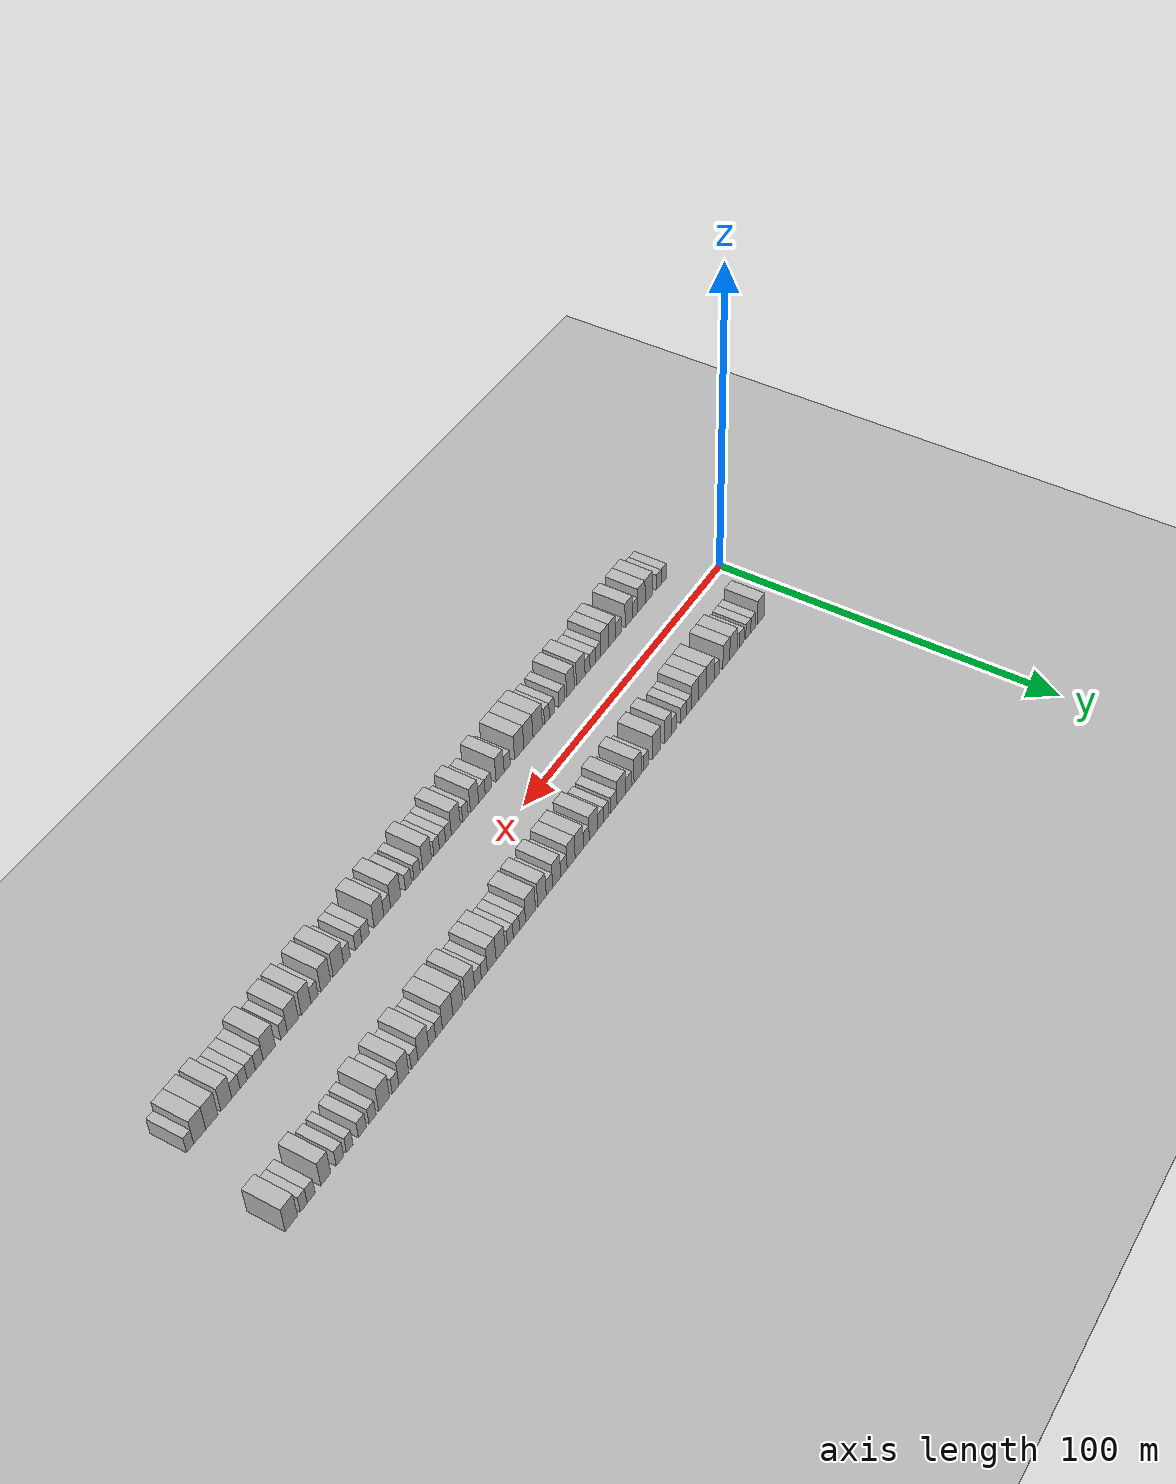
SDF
<?xml version="1.0" encoding="utf-8"?>

<sdf version="1.6">

   <world name="default">

      <gui fullscreen="0">

         <camera name="user_camera">

            <pose>-15 0 4.57585 0 0 0</pose>

            <view_controller>orbit</view_controller>

         </camera>

      </gui>

      <scene>

         <sky>

           <clouds>

             <speed>12</speed>

           </clouds>

         </sky>

         <ambient>0.4 0.4 0.4 1</ambient>

         <background>0.7 0.7 0.7 1</background>

         <shadows>1</shadows>

      </scene>

      <gravity>0 0 -9.8066</gravity>

      <magnetic_field>6e-06 2.3e-05 -4.2e-05</magnetic_field>

      <physics default="0" name="default_physics" type="ode">

         <ode>

            <solver>

               <type>quick</type>

               <iters>10</iters>

               <sor>1.0</sor>

               <use_dynamic_moi_rescaling>0</use_dynamic_moi_rescaling>

            </solver>

            <constraints>

               <cfm>0</cfm>

               <erp>0.2</erp>

               <contact_max_correcting_vel>100</contact_max_correcting_vel>

               <contact_surface_layer>0.001</contact_surface_layer>

            </constraints>

         </ode>

         <max_step_size>0.004</max_step_size>

         <real_time_factor>1</real_time_factor>

         <real_time_update_rate>250</real_time_update_rate>

      </physics>

      <light name="sun" type="directional">

         <cast_shadows>1</cast_shadows>

         <pose>0 0 10 0 0 0</pose>

         <diffuse>0.8 0.8 0.8 1</diffuse>

         <specular>0.2 0.2 0.2 1</specular>

         <attenuation>

            <range>1000</range>

            <constant>0.9</constant>

            <linear>0.01</linear>

            <quadratic>0.001</quadratic>

         </attenuation>

         <direction>-0.5 0.1 -0.9</direction>

      </light>

      <include>

         <name>ground_plane_1</name>

         <uri>model://HANNAS_ground_plane</uri>

         <pose>0 0 0  0 0 0</pose>

      </include>

      <include>

         <name>ground_plane_2</name>

         <uri>model://HANNAS_ground_plane</uri>

         <pose>100 0 0  0 0 0</pose>

      </include>

      <model name="building_1">

         <static>1</static>

         <pose frame="">13.9226 15.0000 0 0.000000 0.000000 1.570796</pose>

         <link name="link">

            <pose frame="">0 0 4.50 0 0 0</pose>

            <collision name="collision">

               <geometry>

                  <box>

                     <size>10.0000 3.8453 9.0000</size>

                  </box>

               </geometry>

               <max_contacts>10</max_contacts>

               <surface>

                  <contact>

                     <ode/>

                  </contact>

                  <bounce/>

                  <friction>

                     <torsional>

                        <ode/>

                     </torsional>

                     <ode/>

                  </friction>

               </surface>

            </collision>

            <visual name="visual">

               <cast_shadows>0</cast_shadows>

               <geometry>

                  <box>

                     <size>10.0000 3.8453 9.0000</size>

                  </box>

               </geometry>

               <material>

                  <script>

                     <uri>model://HANNAS_wall/materials/scripts</uri>

                     <uri>model://HANNAS_wall/materials/textures</uri>

                     <name>vrc/HANNAS_wall</name>

                  </script>

               </material>

            </visual>

            <self_collide>0</self_collide>

            <enable_wind>0</enable_wind>

            <kinematic>0</kinematic>

         </link>

      </model>

      <model name="building_2">

         <static>1</static>

         <pose frame="">18.2007 15.0000 0 0.000000 0.000000 1.570796</pose>

         <link name="link">

            <pose frame="">0 0 3.00 0 0 0</pose>

            <collision name="collision">

               <geometry>

                  <box>

                     <size>10.0000 2.7110 6.0000</size>

                  </box>

               </geometry>

               <max_contacts>10</max_contacts>

               <surface>

                  <contact>

                     <ode/>

                  </contact>

                  <bounce/>

                  <friction>

                     <torsional>

                        <ode/>

                     </torsional>

                     <ode/>

                  </friction>

               </surface>

            </collision>

            <visual name="visual">

               <cast_shadows>0</cast_shadows>

               <geometry>

                  <box>

                     <size>10.0000 2.7110 6.0000</size>

                  </box>

               </geometry>

               <material>

                  <script>

                     <uri>model://HANNAS_wall/materials/scripts</uri>

                     <uri>model://HANNAS_wall/materials/textures</uri>

                     <name>vrc/HANNAS_wall</name>

                  </script>

               </material>

            </visual>

            <self_collide>0</self_collide>

            <enable_wind>0</enable_wind>

            <kinematic>0</kinematic>

         </link>

      </model>

      <model name="building_3">

         <static>1</static>

         <pose frame="">20.9321 15.0000 0 0.000000 0.000000 1.570796</pose>

         <link name="link">

            <pose frame="">0 0 3.00 0 0 0</pose>

            <collision name="collision">

               <geometry>

                  <box>

                     <size>10.0000 2.7518 6.0000</size>

                  </box>

               </geometry>

               <max_contacts>10</max_contacts>

               <surface>

                  <contact>

                     <ode/>

                  </contact>

                  <bounce/>

                  <friction>

                     <torsional>

                        <ode/>

                     </torsional>

                     <ode/>

                  </friction>

               </surface>

            </collision>

            <visual name="visual">

               <cast_shadows>0</cast_shadows>

               <geometry>

                  <box>

                     <size>10.0000 2.7518 6.0000</size>

                  </box>

               </geometry>

               <material>

                  <script>

                     <uri>model://HANNAS_wall/materials/scripts</uri>

                     <uri>model://HANNAS_wall/materials/textures</uri>

                     <name>vrc/HANNAS_wall</name>

                  </script>

               </material>

            </visual>

            <self_collide>0</self_collide>

            <enable_wind>0</enable_wind>

            <kinematic>0</kinematic>

         </link>

      </model>

      <model name="building_4">

         <static>1</static>

         <pose frame="">24.6770 15.0000 0 0.000000 0.000000 1.570796</pose>

         <link name="link">

            <pose frame="">0 0 3.00 0 0 0</pose>

            <collision name="collision">

               <geometry>

                  <box>

                     <size>10.0000 2.7379 6.0000</size>

                  </box>

               </geometry>

               <max_contacts>10</max_contacts>

               <surface>

                  <contact>

                     <ode/>

                  </contact>

                  <bounce/>

                  <friction>

                     <torsional>

                        <ode/>

                     </torsional>

                     <ode/>

                  </friction>

               </surface>

            </collision>

            <visual name="visual">

               <cast_shadows>0</cast_shadows>

               <geometry>

                  <box>

                     <size>10.0000 2.7379 6.0000</size>

                  </box>

               </geometry>

               <material>

                  <script>

                     <uri>model://HANNAS_wall/materials/scripts</uri>

                     <uri>model://HANNAS_wall/materials/textures</uri>

                     <name>vrc/HANNAS_wall</name>

                  </script>

               </material>

            </visual>

            <self_collide>0</self_collide>

            <enable_wind>0</enable_wind>

            <kinematic>0</kinematic>

         </link>

      </model>

      <model name="building_5">

         <static>1</static>

         <pose frame="">29.0868 15.0000 0 0.000000 0.000000 1.570796</pose>

         <link name="link">

            <pose frame="">0 0 4.50 0 0 0</pose>

            <collision name="collision">

               <geometry>

                  <box>

                     <size>10.0000 4.0817 9.0000</size>

                  </box>

               </geometry>

               <max_contacts>10</max_contacts>

               <surface>

                  <contact>

                     <ode/>

                  </contact>

                  <bounce/>

                  <friction>

                     <torsional>

                        <ode/>

                     </torsional>

                     <ode/>

                  </friction>

               </surface>

            </collision>

            <visual name="visual">

               <cast_shadows>0</cast_shadows>

               <geometry>

                  <box>

                     <size>10.0000 4.0817 9.0000</size>

                  </box>

               </geometry>

               <material>

                  <script>

                     <uri>model://HANNAS_wall/materials/scripts</uri>

                     <uri>model://HANNAS_wall/materials/textures</uri>

                     <name>vrc/HANNAS_wall</name>

                  </script>

               </material>

            </visual>

            <self_collide>0</self_collide>

            <enable_wind>0</enable_wind>

            <kinematic>0</kinematic>

         </link>

      </model>

      <model name="building_6">

         <static>1</static>

         <pose frame="">33.0017 15.0000 0 0.000000 0.000000 1.570796</pose>

         <link name="link">

            <pose frame="">0 0 4.50 0 0 0</pose>

            <collision name="collision">

               <geometry>

                  <box>

                     <size>10.0000 3.7479 9.0000</size>

                  </box>

               </geometry>

               <max_contacts>10</max_contacts>

               <surface>

                  <contact>

                     <ode/>

                  </contact>

                  <bounce/>

                  <friction>

                     <torsional>

                        <ode/>

                     </torsional>

                     <ode/>

                  </friction>

               </surface>

            </collision>

            <visual name="visual">

               <cast_shadows>0</cast_shadows>

               <geometry>

                  <box>

                     <size>10.0000 3.7479 9.0000</size>

                  </box>

               </geometry>

               <material>

                  <script>

                     <uri>model://HANNAS_wall/materials/scripts</uri>

                     <uri>model://HANNAS_wall/materials/textures</uri>

                     <name>vrc/HANNAS_wall</name>

                  </script>

               </material>

            </visual>

            <self_collide>0</self_collide>

            <enable_wind>0</enable_wind>

            <kinematic>0</kinematic>

         </link>

      </model>

      <model name="building_7">

         <static>1</static>

         <pose frame="">38.1766 15.0000 0 0.000000 0.000000 1.570796</pose>

         <link name="link">

            <pose frame="">0 0 3.00 0 0 0</pose>

            <collision name="collision">

               <geometry>

                  <box>

                     <size>10.0000 2.6020 6.0000</size>

                  </box>

               </geometry>

               <max_contacts>10</max_contacts>

               <surface>

                  <contact>

                     <ode/>

                  </contact>

                  <bounce/>

                  <friction>

                     <torsional>

                        <ode/>

                     </torsional>

                     <ode/>

                  </friction>

               </surface>

            </collision>

            <visual name="visual">

               <cast_shadows>0</cast_shadows>

               <geometry>

                  <box>

                     <size>10.0000 2.6020 6.0000</size>

                  </box>

               </geometry>

               <material>

                  <script>

                     <uri>model://HANNAS_wall/materials/scripts</uri>

                     <uri>model://HANNAS_wall/materials/textures</uri>

                     <name>vrc/HANNAS_wall</name>

                  </script>

               </material>

            </visual>

            <self_collide>0</self_collide>

            <enable_wind>0</enable_wind>

            <kinematic>0</kinematic>

         </link>

      </model>

      <model name="building_8">

         <static>1</static>

         <pose frame="">41.6271 15.0000 0 0.000000 0.000000 1.570796</pose>

         <link name="link">

            <pose frame="">0 0 4.50 0 0 0</pose>

            <collision name="collision">

               <geometry>

                  <box>

                     <size>10.0000 4.2989 9.0000</size>

                  </box>

               </geometry>

               <max_contacts>10</max_contacts>

               <surface>

                  <contact>

                     <ode/>

                  </contact>

                  <bounce/>

                  <friction>

                     <torsional>

                        <ode/>

                     </torsional>

                     <ode/>

                  </friction>

               </surface>

            </collision>

            <visual name="visual">

               <cast_shadows>0</cast_shadows>

               <geometry>

                  <box>

                     <size>10.0000 4.2989 9.0000</size>

                  </box>

               </geometry>

               <material>

                  <script>

                     <uri>model://HANNAS_wall/materials/scripts</uri>

                     <uri>model://HANNAS_wall/materials/textures</uri>

                     <name>vrc/HANNAS_wall</name>

                  </script>

               </material>

            </visual>

            <self_collide>0</self_collide>

            <enable_wind>0</enable_wind>

            <kinematic>0</kinematic>

         </link>

      </model>

      <model name="building_9">

         <static>1</static>

         <pose frame="">45.7848 15.0000 0 0.000000 0.000000 1.570796</pose>

         <link name="link">

            <pose frame="">0 0 4.50 0 0 0</pose>

            <collision name="collision">

               <geometry>

                  <box>

                     <size>10.0000 4.0166 9.0000</size>

                  </box>

               </geometry>

               <max_contacts>10</max_contacts>

               <surface>

                  <contact>

                     <ode/>

                  </contact>

                  <bounce/>

                  <friction>

                     <torsional>

                        <ode/>

                     </torsional>

                     <ode/>

                  </friction>

               </surface>

            </collision>

            <visual name="visual">

               <cast_shadows>0</cast_shadows>

               <geometry>

                  <box>

                     <size>10.0000 4.0166 9.0000</size>

                  </box>

               </geometry>

               <material>

                  <script>

                     <uri>model://HANNAS_wall/materials/scripts</uri>

                     <uri>model://HANNAS_wall/materials/textures</uri>

                     <name>vrc/HANNAS_wall</name>

                  </script>

               </material>

            </visual>

            <self_collide>0</self_collide>

            <enable_wind>0</enable_wind>

            <kinematic>0</kinematic>

         </link>

      </model>

      <model name="building_10">

         <static>1</static>

         <pose frame="">49.6950 15.0000 0 0.000000 0.000000 1.570796</pose>

         <link name="link">

            <pose frame="">0 0 4.50 0 0 0</pose>

            <collision name="collision">

               <geometry>

                  <box>

                     <size>10.0000 3.8036 9.0000</size>

                  </box>

               </geometry>

               <max_contacts>10</max_contacts>

               <surface>

                  <contact>

                     <ode/>

                  </contact>

                  <bounce/>

                  <friction>

                     <torsional>

                        <ode/>

                     </torsional>

                     <ode/>

                  </friction>

               </surface>

            </collision>

            <visual name="visual">

               <cast_shadows>0</cast_shadows>

               <geometry>

                  <box>

                     <size>10.0000 3.8036 9.0000</size>

                  </box>

               </geometry>

               <material>

                  <script>

                     <uri>model://HANNAS_wall/materials/scripts</uri>

                     <uri>model://HANNAS_wall/materials/textures</uri>

                     <name>vrc/HANNAS_wall</name>

                  </script>

               </material>

            </visual>

            <self_collide>0</self_collide>

            <enable_wind>0</enable_wind>

            <kinematic>0</kinematic>

         </link>

      </model>

      <model name="building_11">

         <static>1</static>

         <pose frame="">52.8609 15.0000 0 0.000000 0.000000 1.570796</pose>

         <link name="link">

            <pose frame="">0 0 3.00 0 0 0</pose>

            <collision name="collision">

               <geometry>

                  <box>

                     <size>10.0000 2.5283 6.0000</size>

                  </box>

               </geometry>

               <max_contacts>10</max_contacts>

               <surface>

                  <contact>

                     <ode/>

                  </contact>

                  <bounce/>

                  <friction>

                     <torsional>

                        <ode/>

                     </torsional>

                     <ode/>

                  </friction>

               </surface>

            </collision>

            <visual name="visual">

               <cast_shadows>0</cast_shadows>

               <geometry>

                  <box>

                     <size>10.0000 2.5283 6.0000</size>

                  </box>

               </geometry>

               <material>

                  <script>

                     <uri>model://HANNAS_wall/materials/scripts</uri>

                     <uri>model://HANNAS_wall/materials/textures</uri>

                     <name>vrc/HANNAS_wall</name>

                  </script>

               </material>

            </visual>

            <self_collide>0</self_collide>

            <enable_wind>0</enable_wind>

            <kinematic>0</kinematic>

         </link>

      </model>

      <model name="building_12">

         <static>1</static>

         <pose frame="">55.6068 15.0000 0 0.000000 0.000000 1.570796</pose>

         <link name="link">

            <pose frame="">0 0 3.00 0 0 0</pose>

            <collision name="collision">

               <geometry>

                  <box>

                     <size>10.0000 2.9635 6.0000</size>

                  </box>

               </geometry>

               <max_contacts>10</max_contacts>

               <surface>

                  <contact>

                     <ode/>

                  </contact>

                  <bounce/>

                  <friction>

                     <torsional>

                        <ode/>

                     </torsional>

                     <ode/>

                  </friction>

               </surface>

            </collision>

            <visual name="visual">

               <cast_shadows>0</cast_shadows>

               <geometry>

                  <box>

                     <size>10.0000 2.9635 6.0000</size>

                  </box>

               </geometry>

               <material>

                  <script>

                     <uri>model://HANNAS_wall/materials/scripts</uri>

                     <uri>model://HANNAS_wall/materials/textures</uri>

                     <name>vrc/HANNAS_wall</name>

                  </script>

               </material>

            </visual>

            <self_collide>0</self_collide>

            <enable_wind>0</enable_wind>

            <kinematic>0</kinematic>

         </link>

      </model>

      <model name="building_13">

         <static>1</static>

         <pose frame="">60.4055 15.0000 0 0.000000 0.000000 1.570796</pose>

         <link name="link">

            <pose frame="">0 0 3.00 0 0 0</pose>

            <collision name="collision">

               <geometry>

                  <box>

                     <size>10.0000 2.6340 6.0000</size>

                  </box>

               </geometry>

               <max_contacts>10</max_contacts>

               <surface>

                  <contact>

                     <ode/>

                  </contact>

                  <bounce/>

                  <friction>

                     <torsional>

                        <ode/>

                     </torsional>

                     <ode/>

                  </friction>

               </surface>

            </collision>

            <visual name="visual">

               <cast_shadows>0</cast_shadows>

               <geometry>

                  <box>

                     <size>10.0000 2.6340 6.0000</size>

                  </box>

               </geometry>

               <material>

                  <script>

                     <uri>model://HANNAS_wall/materials/scripts</uri>

                     <uri>model://HANNAS_wall/materials/textures</uri>

                     <name>vrc/HANNAS_wall</name>

                  </script>

               </material>

            </visual>

            <self_collide>0</self_collide>

            <enable_wind>0</enable_wind>

            <kinematic>0</kinematic>

         </link>

      </model>

      <model name="building_14">

         <static>1</static>

         <pose frame="">63.5333 15.0000 0 0.000000 0.000000 1.570796</pose>

         <link name="link">

            <pose frame="">0 0 4.50 0 0 0</pose>

            <collision name="collision">

               <geometry>

                  <box>

                     <size>10.0000 3.6216 9.0000</size>

                  </box>

               </geometry>

               <max_contacts>10</max_contacts>

               <surface>

                  <contact>

                     <ode/>

                  </contact>

                  <bounce/>

                  <friction>

                     <torsional>

                        <ode/>

                     </torsional>

                     <ode/>

                  </friction>

               </surface>

            </collision>

            <visual name="visual">

               <cast_shadows>0</cast_shadows>

               <geometry>

                  <box>

                     <size>10.0000 3.6216 9.0000</size>

                  </box>

               </geometry>

               <material>

                  <script>

                     <uri>model://HANNAS_wall/materials/scripts</uri>

                     <uri>model://HANNAS_wall/materials/textures</uri>

                     <name>vrc/HANNAS_wall</name>

                  </script>

               </material>

            </visual>

            <self_collide>0</self_collide>

            <enable_wind>0</enable_wind>

            <kinematic>0</kinematic>

         </link>

      </model>

      <model name="building_15">

         <static>1</static>

         <pose frame="">69.4708 15.0000 0 0.000000 0.000000 1.570796</pose>

         <link name="link">

            <pose frame="">0 0 4.50 0 0 0</pose>

            <collision name="collision">

               <geometry>

                  <box>

                     <size>10.0000 4.2534 9.0000</size>

                  </box>

               </geometry>

               <max_contacts>10</max_contacts>

               <surface>

                  <contact>

                     <ode/>

                  </contact>

                  <bounce/>

                  <friction>

                     <torsional>

                        <ode/>

                     </torsional>

                     <ode/>

                  </friction>

               </surface>

            </collision>

            <visual name="visual">

               <cast_shadows>0</cast_shadows>

               <geometry>

                  <box>

                     <size>10.0000 4.2534 9.0000</size>

                  </box>

               </geometry>

               <material>

                  <script>

                     <uri>model://HANNAS_wall/materials/scripts</uri>

                     <uri>model://HANNAS_wall/materials/textures</uri>

                     <name>vrc/HANNAS_wall</name>

                  </script>

               </material>

            </visual>

            <self_collide>0</self_collide>

            <enable_wind>0</enable_wind>

            <kinematic>0</kinematic>

         </link>

      </model>

      <model name="building_16">

         <static>1</static>

         <pose frame="">74.8315 15.0000 0 0.000000 0.000000 1.570796</pose>

         <link name="link">

            <pose frame="">0 0 3.00 0 0 0</pose>

            <collision name="collision">

               <geometry>

                  <box>

                     <size>10.0000 2.4681 6.0000</size>

                  </box>

               </geometry>

               <max_contacts>10</max_contacts>

               <surface>

                  <contact>

                     <ode/>

                  </contact>

                  <bounce/>

                  <friction>

                     <torsional>

                        <ode/>

                     </torsional>

                     <ode/>

                  </friction>

               </surface>

            </collision>

            <visual name="visual">

               <cast_shadows>0</cast_shadows>

               <geometry>

                  <box>

                     <size>10.0000 2.4681 6.0000</size>

                  </box>

               </geometry>

               <material>

                  <script>

                     <uri>model://HANNAS_wall/materials/scripts</uri>

                     <uri>model://HANNAS_wall/materials/textures</uri>

                     <name>vrc/HANNAS_wall</name>

                  </script>

               </material>

            </visual>

            <self_collide>0</self_collide>

            <enable_wind>0</enable_wind>

            <kinematic>0</kinematic>

         </link>

      </model>

      <model name="building_17">

         <static>1</static>

         <pose frame="">78.8737 15.0000 0 0.000000 0.000000 1.570796</pose>

         <link name="link">

            <pose frame="">0 0 4.50 0 0 0</pose>

            <collision name="collision">

               <geometry>

                  <box>

                     <size>10.0000 3.6162 9.0000</size>

                  </box>

               </geometry>

               <max_contacts>10</max_contacts>

               <surface>

                  <contact>

                     <ode/>

                  </contact>

                  <bounce/>

                  <friction>

                     <torsional>

                        <ode/>

                     </torsional>

                     <ode/>

                  </friction>

               </surface>

            </collision>

            <visual name="visual">

               <cast_shadows>0</cast_shadows>

               <geometry>

                  <box>

                     <size>10.0000 3.6162 9.0000</size>

                  </box>

               </geometry>

               <material>

                  <script>

                     <uri>model://HANNAS_wall/materials/scripts</uri>

                     <uri>model://HANNAS_wall/materials/textures</uri>

                     <name>vrc/HANNAS_wall</name>

                  </script>

               </material>

            </visual>

            <self_collide>0</self_collide>

            <enable_wind>0</enable_wind>

            <kinematic>0</kinematic>

         </link>

      </model>

      <model name="building_18">

         <static>1</static>

         <pose frame="">83.1581 15.0000 0 0.000000 0.000000 1.570796</pose>

         <link name="link">

            <pose frame="">0 0 3.00 0 0 0</pose>

            <collision name="collision">

               <geometry>

                  <box>

                     <size>10.0000 2.9525 6.0000</size>

                  </box>

               </geometry>

               <max_contacts>10</max_contacts>

               <surface>

                  <contact>

                     <ode/>

                  </contact>

                  <bounce/>

                  <friction>

                     <torsional>

                        <ode/>

                     </torsional>

                     <ode/>

                  </friction>

               </surface>

            </collision>

            <visual name="visual">

               <cast_shadows>0</cast_shadows>

               <geometry>

                  <box>

                     <size>10.0000 2.9525 6.0000</size>

                  </box>

               </geometry>

               <material>

                  <script>

                     <uri>model://HANNAS_wall/materials/scripts</uri>

                     <uri>model://HANNAS_wall/materials/textures</uri>

                     <name>vrc/HANNAS_wall</name>

                  </script>

               </material>

            </visual>

            <self_collide>0</self_collide>

            <enable_wind>0</enable_wind>

            <kinematic>0</kinematic>

         </link>

      </model>

      <model name="building_19">

         <static>1</static>

         <pose frame="">86.7985 15.0000 0 0.000000 0.000000 1.570796</pose>

         <link name="link">

            <pose frame="">0 0 4.50 0 0 0</pose>

            <collision name="collision">

               <geometry>

                  <box>

                     <size>10.0000 4.3284 9.0000</size>

                  </box>

               </geometry>

               <max_contacts>10</max_contacts>

               <surface>

                  <contact>

                     <ode/>

                  </contact>

                  <bounce/>

                  <friction>

                     <torsional>

                        <ode/>

                     </torsional>

                     <ode/>

                  </friction>

               </surface>

            </collision>

            <visual name="visual">

               <cast_shadows>0</cast_shadows>

               <geometry>

                  <box>

                     <size>10.0000 4.3284 9.0000</size>

                  </box>

               </geometry>

               <material>

                  <script>

                     <uri>model://HANNAS_wall/materials/scripts</uri>

                     <uri>model://HANNAS_wall/materials/textures</uri>

                     <name>vrc/HANNAS_wall</name>

                  </script>

               </material>

            </visual>

            <self_collide>0</self_collide>

            <enable_wind>0</enable_wind>

            <kinematic>0</kinematic>

         </link>

      </model>

      <model name="building_20">

         <static>1</static>

         <pose frame="">90.4593 15.0000 0 0.000000 0.000000 1.570796</pose>

         <link name="link">

            <pose frame="">0 0 3.00 0 0 0</pose>

            <collision name="collision">

               <geometry>

                  <box>

                     <size>10.0000 2.9933 6.0000</size>

                  </box>

               </geometry>

               <max_contacts>10</max_contacts>

               <surface>

                  <contact>

                     <ode/>

                  </contact>

                  <bounce/>

                  <friction>

                     <torsional>

                        <ode/>

                     </torsional>

                     <ode/>

                  </friction>

               </surface>

            </collision>

            <visual name="visual">

               <cast_shadows>0</cast_shadows>

               <geometry>

                  <box>

                     <size>10.0000 2.9933 6.0000</size>

                  </box>

               </geometry>

               <material>

                  <script>

                     <uri>model://HANNAS_wall/materials/scripts</uri>

                     <uri>model://HANNAS_wall/materials/textures</uri>

                     <name>vrc/HANNAS_wall</name>

                  </script>

               </material>

            </visual>

            <self_collide>0</self_collide>

            <enable_wind>0</enable_wind>

            <kinematic>0</kinematic>

         </link>

      </model>

      <model name="building_21">

         <static>1</static>

         <pose frame="">94.1721 15.0000 0 0.000000 0.000000 1.570796</pose>

         <link name="link">

            <pose frame="">0 0 3.00 0 0 0</pose>

            <collision name="collision">

               <geometry>

                  <box>

                     <size>10.0000 2.4321 6.0000</size>

                  </box>

               </geometry>

               <max_contacts>10</max_contacts>

               <surface>

                  <contact>

                     <ode/>

                  </contact>

                  <bounce/>

                  <friction>

                     <torsional>

                        <ode/>

                     </torsional>

                     <ode/>

                  </friction>

               </surface>

            </collision>

            <visual name="visual">

               <cast_shadows>0</cast_shadows>

               <geometry>

                  <box>

                     <size>10.0000 2.4321 6.0000</size>

                  </box>

               </geometry>

               <material>

                  <script>

                     <uri>model://HANNAS_wall/materials/scripts</uri>

                     <uri>model://HANNAS_wall/materials/textures</uri>

                     <name>vrc/HANNAS_wall</name>

                  </script>

               </material>

            </visual>

            <self_collide>0</self_collide>

            <enable_wind>0</enable_wind>

            <kinematic>0</kinematic>

         </link>

      </model>

      <model name="building_22">

         <static>1</static>

         <pose frame="">96.7443 15.0000 0 0.000000 0.000000 1.570796</pose>

         <link name="link">

            <pose frame="">0 0 3.00 0 0 0</pose>

            <collision name="collision">

               <geometry>

                  <box>

                     <size>10.0000 2.7123 6.0000</size>

                  </box>

               </geometry>

               <max_contacts>10</max_contacts>

               <surface>

                  <contact>

                     <ode/>

                  </contact>

                  <bounce/>

                  <friction>

                     <torsional>

                        <ode/>

                     </torsional>

                     <ode/>

                  </friction>

               </surface>

            </collision>

            <visual name="visual">

               <cast_shadows>0</cast_shadows>

               <geometry>

                  <box>

                     <size>10.0000 2.7123 6.0000</size>

                  </box>

               </geometry>

               <material>

                  <script>

                     <uri>model://HANNAS_wall/materials/scripts</uri>

                     <uri>model://HANNAS_wall/materials/textures</uri>

                     <name>vrc/HANNAS_wall</name>

                  </script>

               </material>

            </visual>

            <self_collide>0</self_collide>

            <enable_wind>0</enable_wind>

            <kinematic>0</kinematic>

         </link>

      </model>

      <model name="building_23">

         <static>1</static>

         <pose frame="">100.1131 15.0000 0 0.000000 0.000000 1.570796</pose>

         <link name="link">

            <pose frame="">0 0 4.50 0 0 0</pose>

            <collision name="collision">

               <geometry>

                  <box>

                     <size>10.0000 4.0254 9.0000</size>

                  </box>

               </geometry>

               <max_contacts>10</max_contacts>

               <surface>

                  <contact>

                     <ode/>

                  </contact>

                  <bounce/>

                  <friction>

                     <torsional>

                        <ode/>

                     </torsional>

                     <ode/>

                  </friction>

               </surface>

            </collision>

            <visual name="visual">

               <cast_shadows>0</cast_shadows>

               <geometry>

                  <box>

                     <size>10.0000 4.0254 9.0000</size>

                  </box>

               </geometry>

               <material>

                  <script>

                     <uri>model://HANNAS_wall/materials/scripts</uri>

                     <uri>model://HANNAS_wall/materials/textures</uri>

                     <name>vrc/HANNAS_wall</name>

                  </script>

               </material>

            </visual>

            <self_collide>0</self_collide>

            <enable_wind>0</enable_wind>

            <kinematic>0</kinematic>

         </link>

      </model>

      <model name="building_24">

         <static>1</static>

         <pose frame="">103.4632 15.0000 0 0.000000 0.000000 1.570796</pose>

         <link name="link">

            <pose frame="">0 0 3.00 0 0 0</pose>

            <collision name="collision">

               <geometry>

                  <box>

                     <size>10.0000 2.6749 6.0000</size>

                  </box>

               </geometry>

               <max_contacts>10</max_contacts>

               <surface>

                  <contact>

                     <ode/>

                  </contact>

                  <bounce/>

                  <friction>

                     <torsional>

                        <ode/>

                     </torsional>

                     <ode/>

                  </friction>

               </surface>

            </collision>

            <visual name="visual">

               <cast_shadows>0</cast_shadows>

               <geometry>

                  <box>

                     <size>10.0000 2.6749 6.0000</size>

                  </box>

               </geometry>

               <material>

                  <script>

                     <uri>model://HANNAS_wall/materials/scripts</uri>

                     <uri>model://HANNAS_wall/materials/textures</uri>

                     <name>vrc/HANNAS_wall</name>

                  </script>

               </material>

            </visual>

            <self_collide>0</self_collide>

            <enable_wind>0</enable_wind>

            <kinematic>0</kinematic>

         </link>

      </model>

      <model name="building_25">

         <static>1</static>

         <pose frame="">106.7706 15.0000 0 0.000000 0.000000 1.570796</pose>

         <link name="link">

            <pose frame="">0 0 4.50 0 0 0</pose>

            <collision name="collision">

               <geometry>

                  <box>

                     <size>10.0000 3.9398 9.0000</size>

                  </box>

               </geometry>

               <max_contacts>10</max_contacts>

               <surface>

                  <contact>

                     <ode/>

                  </contact>

                  <bounce/>

                  <friction>

                     <torsional>

                        <ode/>

                     </torsional>

                     <ode/>

                  </friction>

               </surface>

            </collision>

            <visual name="visual">

               <cast_shadows>0</cast_shadows>

               <geometry>

                  <box>

                     <size>10.0000 3.9398 9.0000</size>

                  </box>

               </geometry>

               <material>

                  <script>

                     <uri>model://HANNAS_wall/materials/scripts</uri>

                     <uri>model://HANNAS_wall/materials/textures</uri>

                     <name>vrc/HANNAS_wall</name>

                  </script>

               </material>

            </visual>

            <self_collide>0</self_collide>

            <enable_wind>0</enable_wind>

            <kinematic>0</kinematic>

         </link>

      </model>

      <model name="building_26">

         <static>1</static>

         <pose frame="">110.5769 15.0000 0 0.000000 0.000000 1.570796</pose>

         <link name="link">

            <pose frame="">0 0 4.50 0 0 0</pose>

            <collision name="collision">

               <geometry>

                  <box>

                     <size>10.0000 3.6727 9.0000</size>

                  </box>

               </geometry>

               <max_contacts>10</max_contacts>

               <surface>

                  <contact>

                     <ode/>

                  </contact>

                  <bounce/>

                  <friction>

                     <torsional>

                        <ode/>

                     </torsional>

                     <ode/>

                  </friction>

               </surface>

            </collision>

            <visual name="visual">

               <cast_shadows>0</cast_shadows>

               <geometry>

                  <box>

                     <size>10.0000 3.6727 9.0000</size>

                  </box>

               </geometry>

               <material>

                  <script>

                     <uri>model://HANNAS_wall/materials/scripts</uri>

                     <uri>model://HANNAS_wall/materials/textures</uri>

                     <name>vrc/HANNAS_wall</name>

                  </script>

               </material>

            </visual>

            <self_collide>0</self_collide>

            <enable_wind>0</enable_wind>

            <kinematic>0</kinematic>

         </link>

      </model>

      <model name="building_27">

         <static>1</static>

         <pose frame="">113.8792 15.0000 0 0.000000 0.000000 1.570796</pose>

         <link name="link">

            <pose frame="">0 0 3.00 0 0 0</pose>

            <collision name="collision">

               <geometry>

                  <box>

                     <size>10.0000 2.9318 6.0000</size>

                  </box>

               </geometry>

               <max_contacts>10</max_contacts>

               <surface>

                  <contact>

                     <ode/>

                  </contact>

                  <bounce/>

                  <friction>

                     <torsional>

                        <ode/>

                     </torsional>

                     <ode/>

                  </friction>

               </surface>

            </collision>

            <visual name="visual">

               <cast_shadows>0</cast_shadows>

               <geometry>

                  <box>

                     <size>10.0000 2.9318 6.0000</size>

                  </box>

               </geometry>

               <material>

                  <script>

                     <uri>model://HANNAS_wall/materials/scripts</uri>

                     <uri>model://HANNAS_wall/materials/textures</uri>

                     <name>vrc/HANNAS_wall</name>

                  </script>

               </material>

            </visual>

            <self_collide>0</self_collide>

            <enable_wind>0</enable_wind>

            <kinematic>0</kinematic>

         </link>

      </model>

      <model name="building_28">

         <static>1</static>

         <pose frame="">117.1531 15.0000 0 0.000000 0.000000 1.570796</pose>

         <link name="link">

            <pose frame="">0 0 4.50 0 0 0</pose>

            <collision name="collision">

               <geometry>

                  <box>

                     <size>10.0000 3.6159 9.0000</size>

                  </box>

               </geometry>

               <max_contacts>10</max_contacts>

               <surface>

                  <contact>

                     <ode/>

                  </contact>

                  <bounce/>

                  <friction>

                     <torsional>

                        <ode/>

                     </torsional>

                     <ode/>

                  </friction>

               </surface>

            </collision>

            <visual name="visual">

               <cast_shadows>0</cast_shadows>

               <geometry>

                  <box>

                     <size>10.0000 3.6159 9.0000</size>

                  </box>

               </geometry>

               <material>

                  <script>

                     <uri>model://HANNAS_wall/materials/scripts</uri>

                     <uri>model://HANNAS_wall/materials/textures</uri>

                     <name>vrc/HANNAS_wall</name>

                  </script>

               </material>

            </visual>

            <self_collide>0</self_collide>

            <enable_wind>0</enable_wind>

            <kinematic>0</kinematic>

         </link>

      </model>

      <model name="building_29">

         <static>1</static>

         <pose frame="">120.4234 15.0000 0 0.000000 0.000000 1.570796</pose>

         <link name="link">

            <pose frame="">0 0 3.00 0 0 0</pose>

            <collision name="collision">

               <geometry>

                  <box>

                     <size>10.0000 2.9247 6.0000</size>

                  </box>

               </geometry>

               <max_contacts>10</max_contacts>

               <surface>

                  <contact>

                     <ode/>

                  </contact>

                  <bounce/>

                  <friction>

                     <torsional>

                        <ode/>

                     </torsional>

                     <ode/>

                  </friction>

               </surface>

            </collision>

            <visual name="visual">

               <cast_shadows>0</cast_shadows>

               <geometry>

                  <box>

                     <size>10.0000 2.9247 6.0000</size>

                  </box>

               </geometry>

               <material>

                  <script>

                     <uri>model://HANNAS_wall/materials/scripts</uri>

                     <uri>model://HANNAS_wall/materials/textures</uri>

                     <name>vrc/HANNAS_wall</name>

                  </script>

               </material>

            </visual>

            <self_collide>0</self_collide>

            <enable_wind>0</enable_wind>

            <kinematic>0</kinematic>

         </link>

      </model>

      <model name="building_30">

         <static>1</static>

         <pose frame="">123.7611 15.0000 0 0.000000 0.000000 1.570796</pose>

         <link name="link">

            <pose frame="">0 0 4.50 0 0 0</pose>

            <collision name="collision">

               <geometry>

                  <box>

                     <size>10.0000 3.7508 9.0000</size>

                  </box>

               </geometry>

               <max_contacts>10</max_contacts>

               <surface>

                  <contact>

                     <ode/>

                  </contact>

                  <bounce/>

                  <friction>

                     <torsional>

                        <ode/>

                     </torsional>

                     <ode/>

                  </friction>

               </surface>

            </collision>

            <visual name="visual">

               <cast_shadows>0</cast_shadows>

               <geometry>

                  <box>

                     <size>10.0000 3.7508 9.0000</size>

                  </box>

               </geometry>

               <material>

                  <script>

                     <uri>model://HANNAS_wall/materials/scripts</uri>

                     <uri>model://HANNAS_wall/materials/textures</uri>

                     <name>vrc/HANNAS_wall</name>

                  </script>

               </material>

            </visual>

            <self_collide>0</self_collide>

            <enable_wind>0</enable_wind>

            <kinematic>0</kinematic>

         </link>

      </model>

      <model name="building_31">

         <static>1</static>

         <pose frame="">128.8408 15.0000 0 0.000000 0.000000 1.570796</pose>

         <link name="link">

            <pose frame="">0 0 4.50 0 0 0</pose>

            <collision name="collision">

               <geometry>

                  <box>

                     <size>10.0000 4.4086 9.0000</size>

                  </box>

               </geometry>

               <max_contacts>10</max_contacts>

               <surface>

                  <contact>

                     <ode/>

                  </contact>

                  <bounce/>

                  <friction>

                     <torsional>

                        <ode/>

                     </torsional>

                     <ode/>

                  </friction>

               </surface>

            </collision>

            <visual name="visual">

               <cast_shadows>0</cast_shadows>

               <geometry>

                  <box>

                     <size>10.0000 4.4086 9.0000</size>

                  </box>

               </geometry>

               <material>

                  <script>

                     <uri>model://HANNAS_wall/materials/scripts</uri>

                     <uri>model://HANNAS_wall/materials/textures</uri>

                     <name>vrc/HANNAS_wall</name>

                  </script>

               </material>

            </visual>

            <self_collide>0</self_collide>

            <enable_wind>0</enable_wind>

            <kinematic>0</kinematic>

         </link>

      </model>

      <model name="building_32">

         <static>1</static>

         <pose frame="">132.3393 15.0000 0 0.000000 0.000000 1.570796</pose>

         <link name="link">

            <pose frame="">0 0 3.00 0 0 0</pose>

            <collision name="collision">

               <geometry>

                  <box>

                     <size>10.0000 2.5883 6.0000</size>

                  </box>

               </geometry>

               <max_contacts>10</max_contacts>

               <surface>

                  <contact>

                     <ode/>

                  </contact>

                  <bounce/>

                  <friction>

                     <torsional>

                        <ode/>

                     </torsional>

                     <ode/>

                  </friction>

               </surface>

            </collision>

            <visual name="visual">

               <cast_shadows>0</cast_shadows>

               <geometry>

                  <box>

                     <size>10.0000 2.5883 6.0000</size>

                  </box>

               </geometry>

               <material>

                  <script>

                     <uri>model://HANNAS_wall/materials/scripts</uri>

                     <uri>model://HANNAS_wall/materials/textures</uri>

                     <name>vrc/HANNAS_wall</name>

                  </script>

               </material>

            </visual>

            <self_collide>0</self_collide>

            <enable_wind>0</enable_wind>

            <kinematic>0</kinematic>

         </link>

      </model>

      <model name="building_33">

         <static>1</static>

         <pose frame="">135.0188 15.0000 0 0.000000 0.000000 1.570796</pose>

         <link name="link">

            <pose frame="">0 0 3.00 0 0 0</pose>

            <collision name="collision">

               <geometry>

                  <box>

                     <size>10.0000 2.7707 6.0000</size>

                  </box>

               </geometry>

               <max_contacts>10</max_contacts>

               <surface>

                  <contact>

                     <ode/>

                  </contact>

                  <bounce/>

                  <friction>

                     <torsional>

                        <ode/>

                     </torsional>

                     <ode/>

                  </friction>

               </surface>

            </collision>

            <visual name="visual">

               <cast_shadows>0</cast_shadows>

               <geometry>

                  <box>

                     <size>10.0000 2.7707 6.0000</size>

                  </box>

               </geometry>

               <material>

                  <script>

                     <uri>model://HANNAS_wall/materials/scripts</uri>

                     <uri>model://HANNAS_wall/materials/textures</uri>

                     <name>vrc/HANNAS_wall</name>

                  </script>

               </material>

            </visual>

            <self_collide>0</self_collide>

            <enable_wind>0</enable_wind>

            <kinematic>0</kinematic>

         </link>

      </model>

      <model name="building_34">

         <static>1</static>

         <pose frame="">137.6904 15.0000 0 0.000000 0.000000 1.570796</pose>

         <link name="link">

            <pose frame="">0 0 3.00 0 0 0</pose>

            <collision name="collision">

               <geometry>

                  <box>

                     <size>10.0000 2.5725 6.0000</size>

                  </box>

               </geometry>

               <max_contacts>10</max_contacts>

               <surface>

                  <contact>

                     <ode/>

                  </contact>

                  <bounce/>

                  <friction>

                     <torsional>

                        <ode/>

                     </torsional>

                     <ode/>

                  </friction>

               </surface>

            </collision>

            <visual name="visual">

               <cast_shadows>0</cast_shadows>

               <geometry>

                  <box>

                     <size>10.0000 2.5725 6.0000</size>

                  </box>

               </geometry>

               <material>

                  <script>

                     <uri>model://HANNAS_wall/materials/scripts</uri>

                     <uri>model://HANNAS_wall/materials/textures</uri>

                     <name>vrc/HANNAS_wall</name>

                  </script>

               </material>

            </visual>

            <self_collide>0</self_collide>

            <enable_wind>0</enable_wind>

            <kinematic>0</kinematic>

         </link>

      </model>

      <model name="building_35">

         <static>1</static>

         <pose frame="">141.8845 15.0000 0 0.000000 0.000000 1.570796</pose>

         <link name="link">

            <pose frame="">0 0 4.50 0 0 0</pose>

            <collision name="collision">

               <geometry>

                  <box>

                     <size>10.0000 3.8157 9.0000</size>

                  </box>

               </geometry>

               <max_contacts>10</max_contacts>

               <surface>

                  <contact>

                     <ode/>

                  </contact>

                  <bounce/>

                  <friction>

                     <torsional>

                        <ode/>

                     </torsional>

                     <ode/>

                  </friction>

               </surface>

            </collision>

            <visual name="visual">

               <cast_shadows>0</cast_shadows>

               <geometry>

                  <box>

                     <size>10.0000 3.8157 9.0000</size>

                  </box>

               </geometry>

               <material>

                  <script>

                     <uri>model://HANNAS_wall/materials/scripts</uri>

                     <uri>model://HANNAS_wall/materials/textures</uri>

                     <name>vrc/HANNAS_wall</name>

                  </script>

               </material>

            </visual>

            <self_collide>0</self_collide>

            <enable_wind>0</enable_wind>

            <kinematic>0</kinematic>

         </link>

      </model>

      <model name="building_36">

         <static>1</static>

         <pose frame="">145.6510 15.0000 0 0.000000 0.000000 1.570796</pose>

         <link name="link">

            <pose frame="">0 0 4.50 0 0 0</pose>

            <collision name="collision">

               <geometry>

                  <box>

                     <size>10.0000 3.7173 9.0000</size>

                  </box>

               </geometry>

               <max_contacts>10</max_contacts>

               <surface>

                  <contact>

                     <ode/>

                  </contact>

                  <bounce/>

                  <friction>

                     <torsional>

                        <ode/>

                     </torsional>

                     <ode/>

                  </friction>

               </surface>

            </collision>

            <visual name="visual">

               <cast_shadows>0</cast_shadows>

               <geometry>

                  <box>

                     <size>10.0000 3.7173 9.0000</size>

                  </box>

               </geometry>

               <material>

                  <script>

                     <uri>model://HANNAS_wall/materials/scripts</uri>

                     <uri>model://HANNAS_wall/materials/textures</uri>

                     <name>vrc/HANNAS_wall</name>

                  </script>

               </material>

            </visual>

            <self_collide>0</self_collide>

            <enable_wind>0</enable_wind>

            <kinematic>0</kinematic>

         </link>

      </model>

      <model name="building_37">

         <static>1</static>

         <pose frame="">148.7827 15.0000 0 0.000000 0.000000 1.570796</pose>

         <link name="link">

            <pose frame="">0 0 3.00 0 0 0</pose>

            <collision name="collision">

               <geometry>

                  <box>

                     <size>10.0000 2.5460 6.0000</size>

                  </box>

               </geometry>

               <max_contacts>10</max_contacts>

               <surface>

                  <contact>

                     <ode/>

                  </contact>

                  <bounce/>

                  <friction>

                     <torsional>

                        <ode/>

                     </torsional>

                     <ode/>

                  </friction>

               </surface>

            </collision>

            <visual name="visual">

               <cast_shadows>0</cast_shadows>

               <geometry>

                  <box>

                     <size>10.0000 2.5460 6.0000</size>

                  </box>

               </geometry>

               <material>

                  <script>

                     <uri>model://HANNAS_wall/materials/scripts</uri>

                     <uri>model://HANNAS_wall/materials/textures</uri>

                     <name>vrc/HANNAS_wall</name>

                  </script>

               </material>

            </visual>

            <self_collide>0</self_collide>

            <enable_wind>0</enable_wind>

            <kinematic>0</kinematic>

         </link>

      </model>

      <model name="building_38">

         <static>1</static>

         <pose frame="">151.4500 15.0000 0 0.000000 0.000000 1.570796</pose>

         <link name="link">

            <pose frame="">0 0 3.00 0 0 0</pose>

            <collision name="collision">

               <geometry>

                  <box>

                     <size>10.0000 2.7886 6.0000</size>

                  </box>

               </geometry>

               <max_contacts>10</max_contacts>

               <surface>

                  <contact>

                     <ode/>

                  </contact>

                  <bounce/>

                  <friction>

                     <torsional>

                        <ode/>

                     </torsional>

                     <ode/>

                  </friction>

               </surface>

            </collision>

            <visual name="visual">

               <cast_shadows>0</cast_shadows>

               <geometry>

                  <box>

                     <size>10.0000 2.7886 6.0000</size>

                  </box>

               </geometry>

               <material>

                  <script>

                     <uri>model://HANNAS_wall/materials/scripts</uri>

                     <uri>model://HANNAS_wall/materials/textures</uri>

                     <name>vrc/HANNAS_wall</name>

                  </script>

               </material>

            </visual>

            <self_collide>0</self_collide>

            <enable_wind>0</enable_wind>

            <kinematic>0</kinematic>

         </link>

      </model>

      <model name="building_39">

         <static>1</static>

         <pose frame="">154.8027 15.0000 0 0.000000 0.000000 1.570796</pose>

         <link name="link">

            <pose frame="">0 0 4.50 0 0 0</pose>

            <collision name="collision">

               <geometry>

                  <box>

                     <size>10.0000 3.9167 9.0000</size>

                  </box>

               </geometry>

               <max_contacts>10</max_contacts>

               <surface>

                  <contact>

                     <ode/>

                  </contact>

                  <bounce/>

                  <friction>

                     <torsional>

                        <ode/>

                     </torsional>

                     <ode/>

                  </friction>

               </surface>

            </collision>

            <visual name="visual">

               <cast_shadows>0</cast_shadows>

               <geometry>

                  <box>

                     <size>10.0000 3.9167 9.0000</size>

                  </box>

               </geometry>

               <material>

                  <script>

                     <uri>model://HANNAS_wall/materials/scripts</uri>

                     <uri>model://HANNAS_wall/materials/textures</uri>

                     <name>vrc/HANNAS_wall</name>

                  </script>

               </material>

            </visual>

            <self_collide>0</self_collide>

            <enable_wind>0</enable_wind>

            <kinematic>0</kinematic>

         </link>

      </model>

      <model name="building_40">

         <static>1</static>

         <pose frame="">159.7739 15.0000 0 0.000000 0.000000 1.570796</pose>

         <link name="link">

            <pose frame="">0 0 4.50 0 0 0</pose>

            <collision name="collision">

               <geometry>

                  <box>

                     <size>10.0000 4.0258 9.0000</size>

                  </box>

               </geometry>

               <max_contacts>10</max_contacts>

               <surface>

                  <contact>

                     <ode/>

                  </contact>

                  <bounce/>

                  <friction>

                     <torsional>

                        <ode/>

                     </torsional>

                     <ode/>

                  </friction>

               </surface>

            </collision>

            <visual name="visual">

               <cast_shadows>0</cast_shadows>

               <geometry>

                  <box>

                     <size>10.0000 4.0258 9.0000</size>

                  </box>

               </geometry>

               <material>

                  <script>

                     <uri>model://HANNAS_wall/materials/scripts</uri>

                     <uri>model://HANNAS_wall/materials/textures</uri>

                     <name>vrc/HANNAS_wall</name>

                  </script>

               </material>

            </visual>

            <self_collide>0</self_collide>

            <enable_wind>0</enable_wind>

            <kinematic>0</kinematic>

         </link>

      </model>

      <model name="building_41">

         <static>1</static>

         <pose frame="">163.9372 15.0000 0 0.000000 0.000000 1.570796</pose>

         <link name="link">

            <pose frame="">0 0 4.50 0 0 0</pose>

            <collision name="collision">

               <geometry>

                  <box>

                     <size>10.0000 4.3008 9.0000</size>

                  </box>

               </geometry>

               <max_contacts>10</max_contacts>

               <surface>

                  <contact>

                     <ode/>

                  </contact>

                  <bounce/>

                  <friction>

                     <torsional>

                        <ode/>

                     </torsional>

                     <ode/>

                  </friction>

               </surface>

            </collision>

            <visual name="visual">

               <cast_shadows>0</cast_shadows>

               <geometry>

                  <box>

                     <size>10.0000 4.3008 9.0000</size>

                  </box>

               </geometry>

               <material>

                  <script>

                     <uri>model://HANNAS_wall/materials/scripts</uri>

                     <uri>model://HANNAS_wall/materials/textures</uri>

                     <name>vrc/HANNAS_wall</name>

                  </script>

               </material>

            </visual>

            <self_collide>0</self_collide>

            <enable_wind>0</enable_wind>

            <kinematic>0</kinematic>

         </link>

      </model>

      <model name="building_42">

         <static>1</static>

         <pose frame="">167.4386 15.0000 0 0.000000 0.000000 1.570796</pose>

         <link name="link">

            <pose frame="">0 0 3.00 0 0 0</pose>

            <collision name="collision">

               <geometry>

                  <box>

                     <size>10.0000 2.7020 6.0000</size>

                  </box>

               </geometry>

               <max_contacts>10</max_contacts>

               <surface>

                  <contact>

                     <ode/>

                  </contact>

                  <bounce/>

                  <friction>

                     <torsional>

                        <ode/>

                     </torsional>

                     <ode/>

                  </friction>

               </surface>

            </collision>

            <visual name="visual">

               <cast_shadows>0</cast_shadows>

               <geometry>

                  <box>

                     <size>10.0000 2.7020 6.0000</size>

                  </box>

               </geometry>

               <material>

                  <script>

                     <uri>model://HANNAS_wall/materials/scripts</uri>

                     <uri>model://HANNAS_wall/materials/textures</uri>

                     <name>vrc/HANNAS_wall</name>

                  </script>

               </material>

            </visual>

            <self_collide>0</self_collide>

            <enable_wind>0</enable_wind>

            <kinematic>0</kinematic>

         </link>

      </model>

      <model name="building_43">

         <static>1</static>

         <pose frame="">170.1975 15.0000 0 0.000000 0.000000 1.570796</pose>

         <link name="link">

            <pose frame="">0 0 3.00 0 0 0</pose>

            <collision name="collision">

               <geometry>

                  <box>

                     <size>10.0000 2.8158 6.0000</size>

                  </box>

               </geometry>

               <max_contacts>10</max_contacts>

               <surface>

                  <contact>

                     <ode/>

                  </contact>

                  <bounce/>

                  <friction>

                     <torsional>

                        <ode/>

                     </torsional>

                     <ode/>

                  </friction>

               </surface>

            </collision>

            <visual name="visual">

               <cast_shadows>0</cast_shadows>

               <geometry>

                  <box>

                     <size>10.0000 2.8158 6.0000</size>

                  </box>

               </geometry>

               <material>

                  <script>

                     <uri>model://HANNAS_wall/materials/scripts</uri>

                     <uri>model://HANNAS_wall/materials/textures</uri>

                     <name>vrc/HANNAS_wall</name>

                  </script>

               </material>

            </visual>

            <self_collide>0</self_collide>

            <enable_wind>0</enable_wind>

            <kinematic>0</kinematic>

         </link>

      </model>

      <model name="building_44">

         <static>1</static>

         <pose frame="">173.7236 15.0000 0 0.000000 0.000000 1.570796</pose>

         <link name="link">

            <pose frame="">0 0 4.50 0 0 0</pose>

            <collision name="collision">

               <geometry>

                  <box>

                     <size>10.0000 4.2362 9.0000</size>

                  </box>

               </geometry>

               <max_contacts>10</max_contacts>

               <surface>

                  <contact>

                     <ode/>

                  </contact>

                  <bounce/>

                  <friction>

                     <torsional>

                        <ode/>

                     </torsional>

                     <ode/>

                  </friction>

               </surface>

            </collision>

            <visual name="visual">

               <cast_shadows>0</cast_shadows>

               <geometry>

                  <box>

                     <size>10.0000 4.2362 9.0000</size>

                  </box>

               </geometry>

               <material>

                  <script>

                     <uri>model://HANNAS_wall/materials/scripts</uri>

                     <uri>model://HANNAS_wall/materials/textures</uri>

                     <name>vrc/HANNAS_wall</name>

                  </script>

               </material>

            </visual>

            <self_collide>0</self_collide>

            <enable_wind>0</enable_wind>

            <kinematic>0</kinematic>

         </link>

      </model>

      <model name="building_45">

         <static>1</static>

         <pose frame="">177.1646 15.0000 0 0.000000 0.000000 1.570796</pose>

         <link name="link">

            <pose frame="">0 0 3.00 0 0 0</pose>

            <collision name="collision">

               <geometry>

                  <box>

                     <size>10.0000 2.6458 6.0000</size>

                  </box>

               </geometry>

               <max_contacts>10</max_contacts>

               <surface>

                  <contact>

                     <ode/>

                  </contact>

                  <bounce/>

                  <friction>

                     <torsional>

                        <ode/>

                     </torsional>

                     <ode/>

                  </friction>

               </surface>

            </collision>

            <visual name="visual">

               <cast_shadows>0</cast_shadows>

               <geometry>

                  <box>

                     <size>10.0000 2.6458 6.0000</size>

                  </box>

               </geometry>

               <material>

                  <script>

                     <uri>model://HANNAS_wall/materials/scripts</uri>

                     <uri>model://HANNAS_wall/materials/textures</uri>

                     <name>vrc/HANNAS_wall</name>

                  </script>

               </material>

            </visual>

            <self_collide>0</self_collide>

            <enable_wind>0</enable_wind>

            <kinematic>0</kinematic>

         </link>

      </model>

      <model name="building_46">

         <static>1</static>

         <pose frame="">181.4121 15.0000 0 0.000000 0.000000 1.570796</pose>

         <link name="link">

            <pose frame="">0 0 4.50 0 0 0</pose>

            <collision name="collision">

               <geometry>

                  <box>

                     <size>10.0000 3.8492 9.0000</size>

                  </box>

               </geometry>

               <max_contacts>10</max_contacts>

               <surface>

                  <contact>

                     <ode/>

                  </contact>

                  <bounce/>

                  <friction>

                     <torsional>

                        <ode/>

                     </torsional>

                     <ode/>

                  </friction>

               </surface>

            </collision>

            <visual name="visual">

               <cast_shadows>0</cast_shadows>

               <geometry>

                  <box>

                     <size>10.0000 3.8492 9.0000</size>

                  </box>

               </geometry>

               <material>

                  <script>

                     <uri>model://HANNAS_wall/materials/scripts</uri>

                     <uri>model://HANNAS_wall/materials/textures</uri>

                     <name>vrc/HANNAS_wall</name>

                  </script>

               </material>

            </visual>

            <self_collide>0</self_collide>

            <enable_wind>0</enable_wind>

            <kinematic>0</kinematic>

         </link>

      </model>

      <model name="building_47">

         <static>1</static>

         <pose frame="">184.6428 15.0000 0 0.000000 0.000000 1.570796</pose>

         <link name="link">

            <pose frame="">0 0 3.00 0 0 0</pose>

            <collision name="collision">

               <geometry>

                  <box>

                     <size>10.0000 2.6121 6.0000</size>

                  </box>

               </geometry>

               <max_contacts>10</max_contacts>

               <surface>

                  <contact>

                     <ode/>

                  </contact>

                  <bounce/>

                  <friction>

                     <torsional>

                        <ode/>

                     </torsional>

                     <ode/>

                  </friction>

               </surface>

            </collision>

            <visual name="visual">

               <cast_shadows>0</cast_shadows>

               <geometry>

                  <box>

                     <size>10.0000 2.6121 6.0000</size>

                  </box>

               </geometry>

               <material>

                  <script>

                     <uri>model://HANNAS_wall/materials/scripts</uri>

                     <uri>model://HANNAS_wall/materials/textures</uri>

                     <name>vrc/HANNAS_wall</name>

                  </script>

               </material>

            </visual>

            <self_collide>0</self_collide>

            <enable_wind>0</enable_wind>

            <kinematic>0</kinematic>

         </link>

      </model>

      <model name="building_48">

         <static>1</static>

         <pose frame="">189.0497 15.0000 0 0.000000 0.000000 1.570796</pose>

         <link name="link">

            <pose frame="">0 0 4.50 0 0 0</pose>

            <collision name="collision">

               <geometry>

                  <box>

                     <size>10.0000 4.2017 9.0000</size>

                  </box>

               </geometry>

               <max_contacts>10</max_contacts>

               <surface>

                  <contact>

                     <ode/>

                  </contact>

                  <bounce/>

                  <friction>

                     <torsional>

                        <ode/>

                     </torsional>

                     <ode/>

                  </friction>

               </surface>

            </collision>

            <visual name="visual">

               <cast_shadows>0</cast_shadows>

               <geometry>

                  <box>

                     <size>10.0000 4.2017 9.0000</size>

                  </box>

               </geometry>

               <material>

                  <script>

                     <uri>model://HANNAS_wall/materials/scripts</uri>

                     <uri>model://HANNAS_wall/materials/textures</uri>

                     <name>vrc/HANNAS_wall</name>

                  </script>

               </material>

            </visual>

            <self_collide>0</self_collide>

            <enable_wind>0</enable_wind>

            <kinematic>0</kinematic>

         </link>

      </model>

      <model name="building_49">

         <static>1</static>

         <pose frame="">193.4907 15.0000 0 0.000000 0.000000 1.570796</pose>

         <link name="link">

            <pose frame="">0 0 3.00 0 0 0</pose>

            <collision name="collision">

               <geometry>

                  <box>

                     <size>10.0000 2.6802 6.0000</size>

                  </box>

               </geometry>

               <max_contacts>10</max_contacts>

               <surface>

                  <contact>

                     <ode/>

                  </contact>

                  <bounce/>

                  <friction>

                     <torsional>

                        <ode/>

                     </torsional>

                     <ode/>

                  </friction>

               </surface>

            </collision>

            <visual name="visual">

               <cast_shadows>0</cast_shadows>

               <geometry>

                  <box>

                     <size>10.0000 2.6802 6.0000</size>

                  </box>

               </geometry>

               <material>

                  <script>

                     <uri>model://HANNAS_wall/materials/scripts</uri>

                     <uri>model://HANNAS_wall/materials/textures</uri>

                     <name>vrc/HANNAS_wall</name>

                  </script>

               </material>

            </visual>

            <self_collide>0</self_collide>

            <enable_wind>0</enable_wind>

            <kinematic>0</kinematic>

         </link>

      </model>

      <model name="building_50">

         <static>1</static>

         <pose frame="">197.3285 15.0000 0 0.000000 0.000000 1.570796</pose>

         <link name="link">

            <pose frame="">0 0 3.00 0 0 0</pose>

            <collision name="collision">

               <geometry>

                  <box>

                     <size>10.0000 2.9954 6.0000</size>

                  </box>

               </geometry>

               <max_contacts>10</max_contacts>

               <surface>

                  <contact>

                     <ode/>

                  </contact>

                  <bounce/>

                  <friction>

                     <torsional>

                        <ode/>

                     </torsional>

                     <ode/>

                  </friction>

               </surface>

            </collision>

            <visual name="visual">

               <cast_shadows>0</cast_shadows>

               <geometry>

                  <box>

                     <size>10.0000 2.9954 6.0000</size>

                  </box>

               </geometry>

               <material>

                  <script>

                     <uri>model://HANNAS_wall/materials/scripts</uri>

                     <uri>model://HANNAS_wall/materials/textures</uri>

                     <name>vrc/HANNAS_wall</name>

                  </script>

               </material>

            </visual>

            <self_collide>0</self_collide>

            <enable_wind>0</enable_wind>

            <kinematic>0</kinematic>

         </link>

      </model>

      <model name="building_51">

         <static>1</static>

         <pose frame="">202.0354 15.0000 0 0.000000 0.000000 1.570796</pose>

         <link name="link">

            <pose frame="">0 0 3.00 0 0 0</pose>

            <collision name="collision">

               <geometry>

                  <box>

                     <size>10.0000 2.4184 6.0000</size>

                  </box>

               </geometry>

               <max_contacts>10</max_contacts>

               <surface>

                  <contact>

                     <ode/>

                  </contact>

                  <bounce/>

                  <friction>

                     <torsional>

                        <ode/>

                     </torsional>

                     <ode/>

                  </friction>

               </surface>

            </collision>

            <visual name="visual">

               <cast_shadows>0</cast_shadows>

               <geometry>

                  <box>

                     <size>10.0000 2.4184 6.0000</size>

                  </box>

               </geometry>

               <material>

                  <script>

                     <uri>model://HANNAS_wall/materials/scripts</uri>

                     <uri>model://HANNAS_wall/materials/textures</uri>

                     <name>vrc/HANNAS_wall</name>

                  </script>

               </material>

            </visual>

            <self_collide>0</self_collide>

            <enable_wind>0</enable_wind>

            <kinematic>0</kinematic>

         </link>

      </model>

      <model name="building_52">

         <static>1</static>

         <pose frame="">205.6255 15.0000 0 0.000000 0.000000 1.570796</pose>

         <link name="link">

            <pose frame="">0 0 3.00 0 0 0</pose>

            <collision name="collision">

               <geometry>

                  <box>

                     <size>10.0000 2.7619 6.0000</size>

                  </box>

               </geometry>

               <max_contacts>10</max_contacts>

               <surface>

                  <contact>

                     <ode/>

                  </contact>

                  <bounce/>

                  <friction>

                     <torsional>

                        <ode/>

                     </torsional>

                     <ode/>

                  </friction>

               </surface>

            </collision>

            <visual name="visual">

               <cast_shadows>0</cast_shadows>

               <geometry>

                  <box>

                     <size>10.0000 2.7619 6.0000</size>

                  </box>

               </geometry>

               <material>

                  <script>

                     <uri>model://HANNAS_wall/materials/scripts</uri>

                     <uri>model://HANNAS_wall/materials/textures</uri>

                     <name>vrc/HANNAS_wall</name>

                  </script>

               </material>

            </visual>

            <self_collide>0</self_collide>

            <enable_wind>0</enable_wind>

            <kinematic>0</kinematic>

         </link>

      </model>

      <model name="building_53">

         <static>1</static>

         <pose frame="">210.8117 15.0000 0 0.000000 0.000000 1.570796</pose>

         <link name="link">

            <pose frame="">0 0 4.50 0 0 0</pose>

            <collision name="collision">

               <geometry>

                  <box>

                     <size>10.0000 3.6105 9.0000</size>

                  </box>

               </geometry>

               <max_contacts>10</max_contacts>

               <surface>

                  <contact>

                     <ode/>

                  </contact>

                  <bounce/>

                  <friction>

                     <torsional>

                        <ode/>

                     </torsional>

                     <ode/>

                  </friction>

               </surface>

            </collision>

            <visual name="visual">

               <cast_shadows>0</cast_shadows>

               <geometry>

                  <box>

                     <size>10.0000 3.6105 9.0000</size>

                  </box>

               </geometry>

               <material>

                  <script>

                     <uri>model://HANNAS_wall/materials/scripts</uri>

                     <uri>model://HANNAS_wall/materials/textures</uri>

                     <name>vrc/HANNAS_wall</name>

                  </script>

               </material>

            </visual>

            <self_collide>0</self_collide>

            <enable_wind>0</enable_wind>

            <kinematic>0</kinematic>

         </link>

      </model>

      <model name="building_54">

         <static>1</static>

         <pose frame="">216.0396 15.0000 0 0.000000 0.000000 1.570796</pose>

         <link name="link">

            <pose frame="">0 0 3.00 0 0 0</pose>

            <collision name="collision">

               <geometry>

                  <box>

                     <size>10.0000 2.8452 6.0000</size>

                  </box>

               </geometry>

               <max_contacts>10</max_contacts>

               <surface>

                  <contact>

                     <ode/>

                  </contact>

                  <bounce/>

                  <friction>

                     <torsional>

                        <ode/>

                     </torsional>

                     <ode/>

                  </friction>

               </surface>

            </collision>

            <visual name="visual">

               <cast_shadows>0</cast_shadows>

               <geometry>

                  <box>

                     <size>10.0000 2.8452 6.0000</size>

                  </box>

               </geometry>

               <material>

                  <script>

                     <uri>model://HANNAS_wall/materials/scripts</uri>

                     <uri>model://HANNAS_wall/materials/textures</uri>

                     <name>vrc/HANNAS_wall</name>

                  </script>

               </material>

            </visual>

            <self_collide>0</self_collide>

            <enable_wind>0</enable_wind>

            <kinematic>0</kinematic>

         </link>

      </model>

      <model name="building_55">

         <static>1</static>

         <pose frame="">218.6882 15.0000 0 0.000000 0.000000 1.570796</pose>

         <link name="link">

            <pose frame="">0 0 3.00 0 0 0</pose>

            <collision name="collision">

               <geometry>

                  <box>

                     <size>10.0000 2.4521 6.0000</size>

                  </box>

               </geometry>

               <max_contacts>10</max_contacts>

               <surface>

                  <contact>

                     <ode/>

                  </contact>

                  <bounce/>

                  <friction>

                     <torsional>

                        <ode/>

                     </torsional>

                     <ode/>

                  </friction>

               </surface>

            </collision>

            <visual name="visual">

               <cast_shadows>0</cast_shadows>

               <geometry>

                  <box>

                     <size>10.0000 2.4521 6.0000</size>

                  </box>

               </geometry>

               <material>

                  <script>

                     <uri>model://HANNAS_wall/materials/scripts</uri>

                     <uri>model://HANNAS_wall/materials/textures</uri>

                     <name>vrc/HANNAS_wall</name>

                  </script>

               </material>

            </visual>

            <self_collide>0</self_collide>

            <enable_wind>0</enable_wind>

            <kinematic>0</kinematic>

         </link>

      </model>

      <model name="building_56">

         <static>1</static>

         <pose frame="">223.0905 15.0000 0 0.000000 0.000000 1.570796</pose>

         <link name="link">

            <pose frame="">0 0 4.50 0 0 0</pose>

            <collision name="collision">

               <geometry>

                  <box>

                     <size>10.0000 4.3525 9.0000</size>

                  </box>

               </geometry>

               <max_contacts>10</max_contacts>

               <surface>

                  <contact>

                     <ode/>

                  </contact>

                  <bounce/>

                  <friction>

                     <torsional>

                        <ode/>

                     </torsional>

                     <ode/>

                  </friction>

               </surface>

            </collision>

            <visual name="visual">

               <cast_shadows>0</cast_shadows>

               <geometry>

                  <box>

                     <size>10.0000 4.3525 9.0000</size>

                  </box>

               </geometry>

               <material>

                  <script>

                     <uri>model://HANNAS_wall/materials/scripts</uri>

                     <uri>model://HANNAS_wall/materials/textures</uri>

                     <name>vrc/HANNAS_wall</name>

                  </script>

               </material>

            </visual>

            <self_collide>0</self_collide>

            <enable_wind>0</enable_wind>

            <kinematic>0</kinematic>

         </link>

      </model>

      <model name="building_57">

         <static>1</static>

         <pose frame="">13.4262 -15.0000 0 0.000000 0.000000 1.570796</pose>

         <link name="link">

            <pose frame="">0 0 3.00 0 0 0</pose>

            <collision name="collision">

               <geometry>

                  <box>

                     <size>10.0000 2.8524 6.0000</size>

                  </box>

               </geometry>

               <max_contacts>10</max_contacts>

               <surface>

                  <contact>

                     <ode/>

                  </contact>

                  <bounce/>

                  <friction>

                     <torsional>

                        <ode/>

                     </torsional>

                     <ode/>

                  </friction>

               </surface>

            </collision>

            <visual name="visual">

               <cast_shadows>0</cast_shadows>

               <geometry>

                  <box>

                     <size>10.0000 2.8524 6.0000</size>

                  </box>

               </geometry>

               <material>

                  <script>

                     <uri>model://HANNAS_wall/materials/scripts</uri>

                     <uri>model://HANNAS_wall/materials/textures</uri>

                     <name>vrc/HANNAS_wall</name>

                  </script>

               </material>

            </visual>

            <self_collide>0</self_collide>

            <enable_wind>0</enable_wind>

            <kinematic>0</kinematic>

         </link>

      </model>

      <model name="building_58">

         <static>1</static>

         <pose frame="">16.1058 -15.0000 0 0.000000 0.000000 1.570796</pose>

         <link name="link">

            <pose frame="">0 0 3.00 0 0 0</pose>

            <collision name="collision">

               <geometry>

                  <box>

                     <size>10.0000 2.5069 6.0000</size>

                  </box>

               </geometry>

               <max_contacts>10</max_contacts>

               <surface>

                  <contact>

                     <ode/>

                  </contact>

                  <bounce/>

                  <friction>

                     <torsional>

                        <ode/>

                     </torsional>

                     <ode/>

                  </friction>

               </surface>

            </collision>

            <visual name="visual">

               <cast_shadows>0</cast_shadows>

               <geometry>

                  <box>

                     <size>10.0000 2.5069 6.0000</size>

                  </box>

               </geometry>

               <material>

                  <script>

                     <uri>model://HANNAS_wall/materials/scripts</uri>

                     <uri>model://HANNAS_wall/materials/textures</uri>

                     <name>vrc/HANNAS_wall</name>

                  </script>

               </material>

            </visual>

            <self_collide>0</self_collide>

            <enable_wind>0</enable_wind>

            <kinematic>0</kinematic>

         </link>

      </model>

      <model name="building_59">

         <static>1</static>

         <pose frame="">21.4099 -15.0000 0 0.000000 0.000000 1.570796</pose>

         <link name="link">

            <pose frame="">0 0 4.50 0 0 0</pose>

            <collision name="collision">

               <geometry>

                  <box>

                     <size>10.0000 4.1012 9.0000</size>

                  </box>

               </geometry>

               <max_contacts>10</max_contacts>

               <surface>

                  <contact>

                     <ode/>

                  </contact>

                  <bounce/>

                  <friction>

                     <torsional>

                        <ode/>

                     </torsional>

                     <ode/>

                  </friction>

               </surface>

            </collision>

            <visual name="visual">

               <cast_shadows>0</cast_shadows>

               <geometry>

                  <box>

                     <size>10.0000 4.1012 9.0000</size>

                  </box>

               </geometry>

               <material>

                  <script>

                     <uri>model://HANNAS_wall/materials/scripts</uri>

                     <uri>model://HANNAS_wall/materials/textures</uri>

                     <name>vrc/HANNAS_wall</name>

                  </script>

               </material>

            </visual>

            <self_collide>0</self_collide>

            <enable_wind>0</enable_wind>

            <kinematic>0</kinematic>

         </link>

      </model>

      <model name="building_60">

         <static>1</static>

         <pose frame="">25.4114 -15.0000 0 0.000000 0.000000 1.570796</pose>

         <link name="link">

            <pose frame="">0 0 4.50 0 0 0</pose>

            <collision name="collision">

               <geometry>

                  <box>

                     <size>10.0000 3.9020 9.0000</size>

                  </box>

               </geometry>

               <max_contacts>10</max_contacts>

               <surface>

                  <contact>

                     <ode/>

                  </contact>

                  <bounce/>

                  <friction>

                     <torsional>

                        <ode/>

                     </torsional>

                     <ode/>

                  </friction>

               </surface>

            </collision>

            <visual name="visual">

               <cast_shadows>0</cast_shadows>

               <geometry>

                  <box>

                     <size>10.0000 3.9020 9.0000</size>

                  </box>

               </geometry>

               <material>

                  <script>

                     <uri>model://HANNAS_wall/materials/scripts</uri>

                     <uri>model://HANNAS_wall/materials/textures</uri>

                     <name>vrc/HANNAS_wall</name>

                  </script>

               </material>

            </visual>

            <self_collide>0</self_collide>

            <enable_wind>0</enable_wind>

            <kinematic>0</kinematic>

         </link>

      </model>

      <model name="building_61">

         <static>1</static>

         <pose frame="">28.7406 -15.0000 0 0.000000 0.000000 1.570796</pose>

         <link name="link">

            <pose frame="">0 0 3.00 0 0 0</pose>

            <collision name="collision">

               <geometry>

                  <box>

                     <size>10.0000 2.7563 6.0000</size>

                  </box>

               </geometry>

               <max_contacts>10</max_contacts>

               <surface>

                  <contact>

                     <ode/>

                  </contact>

                  <bounce/>

                  <friction>

                     <torsional>

                        <ode/>

                     </torsional>

                     <ode/>

                  </friction>

               </surface>

            </collision>

            <visual name="visual">

               <cast_shadows>0</cast_shadows>

               <geometry>

                  <box>

                     <size>10.0000 2.7563 6.0000</size>

                  </box>

               </geometry>

               <material>

                  <script>

                     <uri>model://HANNAS_wall/materials/scripts</uri>

                     <uri>model://HANNAS_wall/materials/textures</uri>

                     <name>vrc/HANNAS_wall</name>

                  </script>

               </material>

            </visual>

            <self_collide>0</self_collide>

            <enable_wind>0</enable_wind>

            <kinematic>0</kinematic>

         </link>

      </model>

      <model name="building_62">

         <static>1</static>

         <pose frame="">32.0567 -15.0000 0 0.000000 0.000000 1.570796</pose>

         <link name="link">

            <pose frame="">0 0 4.50 0 0 0</pose>

            <collision name="collision">

               <geometry>

                  <box>

                     <size>10.0000 3.8760 9.0000</size>

                  </box>

               </geometry>

               <max_contacts>10</max_contacts>

               <surface>

                  <contact>

                     <ode/>

                  </contact>

                  <bounce/>

                  <friction>

                     <torsional>

                        <ode/>

                     </torsional>

                     <ode/>

                  </friction>

               </surface>

            </collision>

            <visual name="visual">

               <cast_shadows>0</cast_shadows>

               <geometry>

                  <box>

                     <size>10.0000 3.8760 9.0000</size>

                  </box>

               </geometry>

               <material>

                  <script>

                     <uri>model://HANNAS_wall/materials/scripts</uri>

                     <uri>model://HANNAS_wall/materials/textures</uri>

                     <name>vrc/HANNAS_wall</name>

                  </script>

               </material>

            </visual>

            <self_collide>0</self_collide>

            <enable_wind>0</enable_wind>

            <kinematic>0</kinematic>

         </link>

      </model>

      <model name="building_63">

         <static>1</static>

         <pose frame="">37.4647 -15.0000 0 0.000000 0.000000 1.570796</pose>

         <link name="link">

            <pose frame="">0 0 3.00 0 0 0</pose>

            <collision name="collision">

               <geometry>

                  <box>

                     <size>10.0000 2.9399 6.0000</size>

                  </box>

               </geometry>

               <max_contacts>10</max_contacts>

               <surface>

                  <contact>

                     <ode/>

                  </contact>

                  <bounce/>

                  <friction>

                     <torsional>

                        <ode/>

                     </torsional>

                     <ode/>

                  </friction>

               </surface>

            </collision>

            <visual name="visual">

               <cast_shadows>0</cast_shadows>

               <geometry>

                  <box>

                     <size>10.0000 2.9399 6.0000</size>

                  </box>

               </geometry>

               <material>

                  <script>

                     <uri>model://HANNAS_wall/materials/scripts</uri>

                     <uri>model://HANNAS_wall/materials/textures</uri>

                     <name>vrc/HANNAS_wall</name>

                  </script>

               </material>

            </visual>

            <self_collide>0</self_collide>

            <enable_wind>0</enable_wind>

            <kinematic>0</kinematic>

         </link>

      </model>

      <model name="building_64">

         <static>1</static>

         <pose frame="">40.7712 -15.0000 0 0.000000 0.000000 1.570796</pose>

         <link name="link">

            <pose frame="">0 0 4.50 0 0 0</pose>

            <collision name="collision">

               <geometry>

                  <box>

                     <size>10.0000 3.6730 9.0000</size>

                  </box>

               </geometry>

               <max_contacts>10</max_contacts>

               <surface>

                  <contact>

                     <ode/>

                  </contact>

                  <bounce/>

                  <friction>

                     <torsional>

                        <ode/>

                     </torsional>

                     <ode/>

                  </friction>

               </surface>

            </collision>

            <visual name="visual">

               <cast_shadows>0</cast_shadows>

               <geometry>

                  <box>

                     <size>10.0000 3.6730 9.0000</size>

                  </box>

               </geometry>

               <material>

                  <script>

                     <uri>model://HANNAS_wall/materials/scripts</uri>

                     <uri>model://HANNAS_wall/materials/textures</uri>

                     <name>vrc/HANNAS_wall</name>

                  </script>

               </material>

            </visual>

            <self_collide>0</self_collide>

            <enable_wind>0</enable_wind>

            <kinematic>0</kinematic>

         </link>

      </model>

      <model name="building_65">

         <static>1</static>

         <pose frame="">44.5831 -15.0000 0 0.000000 0.000000 1.570796</pose>

         <link name="link">

            <pose frame="">0 0 4.50 0 0 0</pose>

            <collision name="collision">

               <geometry>

                  <box>

                     <size>10.0000 3.9509 9.0000</size>

                  </box>

               </geometry>

               <max_contacts>10</max_contacts>

               <surface>

                  <contact>

                     <ode/>

                  </contact>

                  <bounce/>

                  <friction>

                     <torsional>

                        <ode/>

                     </torsional>

                     <ode/>

                  </friction>

               </surface>

            </collision>

            <visual name="visual">

               <cast_shadows>0</cast_shadows>

               <geometry>

                  <box>

                     <size>10.0000 3.9509 9.0000</size>

                  </box>

               </geometry>

               <material>

                  <script>

                     <uri>model://HANNAS_wall/materials/scripts</uri>

                     <uri>model://HANNAS_wall/materials/textures</uri>

                     <name>vrc/HANNAS_wall</name>

                  </script>

               </material>

            </visual>

            <self_collide>0</self_collide>

            <enable_wind>0</enable_wind>

            <kinematic>0</kinematic>

         </link>

      </model>

      <model name="building_66">

         <static>1</static>

         <pose frame="">47.8256 -15.0000 0 0.000000 0.000000 1.570796</pose>

         <link name="link">

            <pose frame="">0 0 3.00 0 0 0</pose>

            <collision name="collision">

               <geometry>

                  <box>

                     <size>10.0000 2.5341 6.0000</size>

                  </box>

               </geometry>

               <max_contacts>10</max_contacts>

               <surface>

                  <contact>

                     <ode/>

                  </contact>

                  <bounce/>

                  <friction>

                     <torsional>

                        <ode/>

                     </torsional>

                     <ode/>

                  </friction>

               </surface>

            </collision>

            <visual name="visual">

               <cast_shadows>0</cast_shadows>

               <geometry>

                  <box>

                     <size>10.0000 2.5341 6.0000</size>

                  </box>

               </geometry>

               <material>

                  <script>

                     <uri>model://HANNAS_wall/materials/scripts</uri>

                     <uri>model://HANNAS_wall/materials/textures</uri>

                     <name>vrc/HANNAS_wall</name>

                  </script>

               </material>

            </visual>

            <self_collide>0</self_collide>

            <enable_wind>0</enable_wind>

            <kinematic>0</kinematic>

         </link>

      </model>

      <model name="building_67">

         <static>1</static>

         <pose frame="">50.5772 -15.0000 0 0.000000 0.000000 1.570796</pose>

         <link name="link">

            <pose frame="">0 0 3.00 0 0 0</pose>

            <collision name="collision">

               <geometry>

                  <box>

                     <size>10.0000 2.9689 6.0000</size>

                  </box>

               </geometry>

               <max_contacts>10</max_contacts>

               <surface>

                  <contact>

                     <ode/>

                  </contact>

                  <bounce/>

                  <friction>

                     <torsional>

                        <ode/>

                     </torsional>

                     <ode/>

                  </friction>

               </surface>

            </collision>

            <visual name="visual">

               <cast_shadows>0</cast_shadows>

               <geometry>

                  <box>

                     <size>10.0000 2.9689 6.0000</size>

                  </box>

               </geometry>

               <material>

                  <script>

                     <uri>model://HANNAS_wall/materials/scripts</uri>

                     <uri>model://HANNAS_wall/materials/textures</uri>

                     <name>vrc/HANNAS_wall</name>

                  </script>

               </material>

            </visual>

            <self_collide>0</self_collide>

            <enable_wind>0</enable_wind>

            <kinematic>0</kinematic>

         </link>

      </model>

      <model name="building_68">

         <static>1</static>

         <pose frame="">53.3177 -15.0000 0 0.000000 0.000000 1.570796</pose>

         <link name="link">

            <pose frame="">0 0 3.00 0 0 0</pose>

            <collision name="collision">

               <geometry>

                  <box>

                     <size>10.0000 2.5122 6.0000</size>

                  </box>

               </geometry>

               <max_contacts>10</max_contacts>

               <surface>

                  <contact>

                     <ode/>

                  </contact>

                  <bounce/>

                  <friction>

                     <torsional>

                        <ode/>

                     </torsional>

                     <ode/>

                  </friction>

               </surface>

            </collision>

            <visual name="visual">

               <cast_shadows>0</cast_shadows>

               <geometry>

                  <box>

                     <size>10.0000 2.5122 6.0000</size>

                  </box>

               </geometry>

               <material>

                  <script>

                     <uri>model://HANNAS_wall/materials/scripts</uri>

                     <uri>model://HANNAS_wall/materials/textures</uri>

                     <name>vrc/HANNAS_wall</name>

                  </script>

               </material>

            </visual>

            <self_collide>0</self_collide>

            <enable_wind>0</enable_wind>

            <kinematic>0</kinematic>

         </link>

      </model>

      <model name="building_69">

         <static>1</static>

         <pose frame="">56.7246 -15.0000 0 0.000000 0.000000 1.570796</pose>

         <link name="link">

            <pose frame="">0 0 4.50 0 0 0</pose>

            <collision name="collision">

               <geometry>

                  <box>

                     <size>10.0000 4.3016 9.0000</size>

                  </box>

               </geometry>

               <max_contacts>10</max_contacts>

               <surface>

                  <contact>

                     <ode/>

                  </contact>

                  <bounce/>

                  <friction>

                     <torsional>

                        <ode/>

                     </torsional>

                     <ode/>

                  </friction>

               </surface>

            </collision>

            <visual name="visual">

               <cast_shadows>0</cast_shadows>

               <geometry>

                  <box>

                     <size>10.0000 4.3016 9.0000</size>

                  </box>

               </geometry>

               <material>

                  <script>

                     <uri>model://HANNAS_wall/materials/scripts</uri>

                     <uri>model://HANNAS_wall/materials/textures</uri>

                     <name>vrc/HANNAS_wall</name>

                  </script>

               </material>

            </visual>

            <self_collide>0</self_collide>

            <enable_wind>0</enable_wind>

            <kinematic>0</kinematic>

         </link>

      </model>

      <model name="building_70">

         <static>1</static>

         <pose frame="">61.7794 -15.0000 0 0.000000 0.000000 1.570796</pose>

         <link name="link">

            <pose frame="">0 0 4.50 0 0 0</pose>

            <collision name="collision">

               <geometry>

                  <box>

                     <size>10.0000 3.8079 9.0000</size>

                  </box>

               </geometry>

               <max_contacts>10</max_contacts>

               <surface>

                  <contact>

                     <ode/>

                  </contact>

                  <bounce/>

                  <friction>

                     <torsional>

                        <ode/>

                     </torsional>

                     <ode/>

                  </friction>

               </surface>

            </collision>

            <visual name="visual">

               <cast_shadows>0</cast_shadows>

               <geometry>

                  <box>

                     <size>10.0000 3.8079 9.0000</size>

                  </box>

               </geometry>

               <material>

                  <script>

                     <uri>model://HANNAS_wall/materials/scripts</uri>

                     <uri>model://HANNAS_wall/materials/textures</uri>

                     <name>vrc/HANNAS_wall</name>

                  </script>

               </material>

            </visual>

            <self_collide>0</self_collide>

            <enable_wind>0</enable_wind>

            <kinematic>0</kinematic>

         </link>

      </model>

      <model name="building_71">

         <static>1</static>

         <pose frame="">66.1522 -15.0000 0 0.000000 0.000000 1.570796</pose>

         <link name="link">

            <pose frame="">0 0 3.00 0 0 0</pose>

            <collision name="collision">

               <geometry>

                  <box>

                     <size>10.0000 2.9377 6.0000</size>

                  </box>

               </geometry>

               <max_contacts>10</max_contacts>

               <surface>

                  <contact>

                     <ode/>

                  </contact>

                  <bounce/>

                  <friction>

                     <torsional>

                        <ode/>

                     </torsional>

                     <ode/>

                  </friction>

               </surface>

            </collision>

            <visual name="visual">

               <cast_shadows>0</cast_shadows>

               <geometry>

                  <box>

                     <size>10.0000 2.9377 6.0000</size>

                  </box>

               </geometry>

               <material>

                  <script>

                     <uri>model://HANNAS_wall/materials/scripts</uri>

                     <uri>model://HANNAS_wall/materials/textures</uri>

                     <name>vrc/HANNAS_wall</name>

                  </script>

               </material>

            </visual>

            <self_collide>0</self_collide>

            <enable_wind>0</enable_wind>

            <kinematic>0</kinematic>

         </link>

      </model>

      <model name="building_72">

         <static>1</static>

         <pose frame="">70.8683 -15.0000 0 0.000000 0.000000 1.570796</pose>

         <link name="link">

            <pose frame="">0 0 3.00 0 0 0</pose>

            <collision name="collision">

               <geometry>

                  <box>

                     <size>10.0000 2.4945 6.0000</size>

                  </box>

               </geometry>

               <max_contacts>10</max_contacts>

               <surface>

                  <contact>

                     <ode/>

                  </contact>

                  <bounce/>

                  <friction>

                     <torsional>

                        <ode/>

                     </torsional>

                     <ode/>

                  </friction>

               </surface>

            </collision>

            <visual name="visual">

               <cast_shadows>0</cast_shadows>

               <geometry>

                  <box>

                     <size>10.0000 2.4945 6.0000</size>

                  </box>

               </geometry>

               <material>

                  <script>

                     <uri>model://HANNAS_wall/materials/scripts</uri>

                     <uri>model://HANNAS_wall/materials/textures</uri>

                     <name>vrc/HANNAS_wall</name>

                  </script>

               </material>

            </visual>

            <self_collide>0</self_collide>

            <enable_wind>0</enable_wind>

            <kinematic>0</kinematic>

         </link>

      </model>

      <model name="building_73">

         <static>1</static>

         <pose frame="">73.3175 -15.0000 0 0.000000 0.000000 1.570796</pose>

         <link name="link">

            <pose frame="">0 0 3.00 0 0 0</pose>

            <collision name="collision">

               <geometry>

                  <box>

                     <size>10.0000 2.4040 6.0000</size>

                  </box>

               </geometry>

               <max_contacts>10</max_contacts>

               <surface>

                  <contact>

                     <ode/>

                  </contact>

                  <bounce/>

                  <friction>

                     <torsional>

                        <ode/>

                     </torsional>

                     <ode/>

                  </friction>

               </surface>

            </collision>

            <visual name="visual">

               <cast_shadows>0</cast_shadows>

               <geometry>

                  <box>

                     <size>10.0000 2.4040 6.0000</size>

                  </box>

               </geometry>

               <material>

                  <script>

                     <uri>model://HANNAS_wall/materials/scripts</uri>

                     <uri>model://HANNAS_wall/materials/textures</uri>

                     <name>vrc/HANNAS_wall</name>

                  </script>

               </material>

            </visual>

            <self_collide>0</self_collide>

            <enable_wind>0</enable_wind>

            <kinematic>0</kinematic>

         </link>

      </model>

      <model name="building_74">

         <static>1</static>

         <pose frame="">77.7529 -15.0000 0 0.000000 0.000000 1.570796</pose>

         <link name="link">

            <pose frame="">0 0 4.50 0 0 0</pose>

            <collision name="collision">

               <geometry>

                  <box>

                     <size>10.0000 4.4667 9.0000</size>

                  </box>

               </geometry>

               <max_contacts>10</max_contacts>

               <surface>

                  <contact>

                     <ode/>

                  </contact>

                  <bounce/>

                  <friction>

                     <torsional>

                        <ode/>

                     </torsional>

                     <ode/>

                  </friction>

               </surface>

            </collision>

            <visual name="visual">

               <cast_shadows>0</cast_shadows>

               <geometry>

                  <box>

                     <size>10.0000 4.4667 9.0000</size>

                  </box>

               </geometry>

               <material>

                  <script>

                     <uri>model://HANNAS_wall/materials/scripts</uri>

                     <uri>model://HANNAS_wall/materials/textures</uri>

                     <name>vrc/HANNAS_wall</name>

                  </script>

               </material>

            </visual>

            <self_collide>0</self_collide>

            <enable_wind>0</enable_wind>

            <kinematic>0</kinematic>

         </link>

      </model>

      <model name="building_75">

         <static>1</static>

         <pose frame="">82.1399 -15.0000 0 0.000000 0.000000 1.570796</pose>

         <link name="link">

            <pose frame="">0 0 4.50 0 0 0</pose>

            <collision name="collision">

               <geometry>

                  <box>

                     <size>10.0000 4.3073 9.0000</size>

                  </box>

               </geometry>

               <max_contacts>10</max_contacts>

               <surface>

                  <contact>

                     <ode/>

                  </contact>

                  <bounce/>

                  <friction>

                     <torsional>

                        <ode/>

                     </torsional>

                     <ode/>

                  </friction>

               </surface>

            </collision>

            <visual name="visual">

               <cast_shadows>0</cast_shadows>

               <geometry>

                  <box>

                     <size>10.0000 4.3073 9.0000</size>

                  </box>

               </geometry>

               <material>

                  <script>

                     <uri>model://HANNAS_wall/materials/scripts</uri>

                     <uri>model://HANNAS_wall/materials/textures</uri>

                     <name>vrc/HANNAS_wall</name>

                  </script>

               </material>

            </visual>

            <self_collide>0</self_collide>

            <enable_wind>0</enable_wind>

            <kinematic>0</kinematic>

         </link>

      </model>

      <model name="building_76">

         <static>1</static>

         <pose frame="">86.4755 -15.0000 0 0.000000 0.000000 1.570796</pose>

         <link name="link">

            <pose frame="">0 0 4.50 0 0 0</pose>

            <collision name="collision">

               <geometry>

                  <box>

                     <size>10.0000 4.3640 9.0000</size>

                  </box>

               </geometry>

               <max_contacts>10</max_contacts>

               <surface>

                  <contact>

                     <ode/>

                  </contact>

                  <bounce/>

                  <friction>

                     <torsional>

                        <ode/>

                     </torsional>

                     <ode/>

                  </friction>

               </surface>

            </collision>

            <visual name="visual">

               <cast_shadows>0</cast_shadows>

               <geometry>

                  <box>

                     <size>10.0000 4.3640 9.0000</size>

                  </box>

               </geometry>

               <material>

                  <script>

                     <uri>model://HANNAS_wall/materials/scripts</uri>

                     <uri>model://HANNAS_wall/materials/textures</uri>

                     <name>vrc/HANNAS_wall</name>

                  </script>

               </material>

            </visual>

            <self_collide>0</self_collide>

            <enable_wind>0</enable_wind>

            <kinematic>0</kinematic>

         </link>

      </model>

      <model name="building_77">

         <static>1</static>

         <pose frame="">92.0766 -15.0000 0 0.000000 0.000000 1.570796</pose>

         <link name="link">

            <pose frame="">0 0 3.00 0 0 0</pose>

            <collision name="collision">

               <geometry>

                  <box>

                     <size>10.0000 2.8382 6.0000</size>

                  </box>

               </geometry>

               <max_contacts>10</max_contacts>

               <surface>

                  <contact>

                     <ode/>

                  </contact>

                  <bounce/>

                  <friction>

                     <torsional>

                        <ode/>

                     </torsional>

                     <ode/>

                  </friction>

               </surface>

            </collision>

            <visual name="visual">

               <cast_shadows>0</cast_shadows>

               <geometry>

                  <box>

                     <size>10.0000 2.8382 6.0000</size>

                  </box>

               </geometry>

               <material>

                  <script>

                     <uri>model://HANNAS_wall/materials/scripts</uri>

                     <uri>model://HANNAS_wall/materials/textures</uri>

                     <name>vrc/HANNAS_wall</name>

                  </script>

               </material>

            </visual>

            <self_collide>0</self_collide>

            <enable_wind>0</enable_wind>

            <kinematic>0</kinematic>

         </link>

      </model>

      <model name="building_78">

         <static>1</static>

         <pose frame="">95.3479 -15.0000 0 0.000000 0.000000 1.570796</pose>

         <link name="link">

            <pose frame="">0 0 4.50 0 0 0</pose>

            <collision name="collision">

               <geometry>

                  <box>

                     <size>10.0000 3.7043 9.0000</size>

                  </box>

               </geometry>

               <max_contacts>10</max_contacts>

               <surface>

                  <contact>

                     <ode/>

                  </contact>

                  <bounce/>

                  <friction>

                     <torsional>

                        <ode/>

                     </torsional>

                     <ode/>

                  </friction>

               </surface>

            </collision>

            <visual name="visual">

               <cast_shadows>0</cast_shadows>

               <geometry>

                  <box>

                     <size>10.0000 3.7043 9.0000</size>

                  </box>

               </geometry>

               <material>

                  <script>

                     <uri>model://HANNAS_wall/materials/scripts</uri>

                     <uri>model://HANNAS_wall/materials/textures</uri>

                     <name>vrc/HANNAS_wall</name>

                  </script>

               </material>

            </visual>

            <self_collide>0</self_collide>

            <enable_wind>0</enable_wind>

            <kinematic>0</kinematic>

         </link>

      </model>

      <model name="building_79">

         <static>1</static>

         <pose frame="">100.6628 -15.0000 0 0.000000 0.000000 1.570796</pose>

         <link name="link">

            <pose frame="">0 0 3.00 0 0 0</pose>

            <collision name="collision">

               <geometry>

                  <box>

                     <size>10.0000 2.9256 6.0000</size>

                  </box>

               </geometry>

               <max_contacts>10</max_contacts>

               <surface>

                  <contact>

                     <ode/>

                  </contact>

                  <bounce/>

                  <friction>

                     <torsional>

                        <ode/>

                     </torsional>

                     <ode/>

                  </friction>

               </surface>

            </collision>

            <visual name="visual">

               <cast_shadows>0</cast_shadows>

               <geometry>

                  <box>

                     <size>10.0000 2.9256 6.0000</size>

                  </box>

               </geometry>

               <material>

                  <script>

                     <uri>model://HANNAS_wall/materials/scripts</uri>

                     <uri>model://HANNAS_wall/materials/textures</uri>

                     <name>vrc/HANNAS_wall</name>

                  </script>

               </material>

            </visual>

            <self_collide>0</self_collide>

            <enable_wind>0</enable_wind>

            <kinematic>0</kinematic>

         </link>

      </model>

      <model name="building_80">

         <static>1</static>

         <pose frame="">103.6089 -15.0000 0 0.000000 0.000000 1.570796</pose>

         <link name="link">

            <pose frame="">0 0 3.00 0 0 0</pose>

            <collision name="collision">

               <geometry>

                  <box>

                     <size>10.0000 2.9667 6.0000</size>

                  </box>

               </geometry>

               <max_contacts>10</max_contacts>

               <surface>

                  <contact>

                     <ode/>

                  </contact>

                  <bounce/>

                  <friction>

                     <torsional>

                        <ode/>

                     </torsional>

                     <ode/>

                  </friction>

               </surface>

            </collision>

            <visual name="visual">

               <cast_shadows>0</cast_shadows>

               <geometry>

                  <box>

                     <size>10.0000 2.9667 6.0000</size>

                  </box>

               </geometry>

               <material>

                  <script>

                     <uri>model://HANNAS_wall/materials/scripts</uri>

                     <uri>model://HANNAS_wall/materials/textures</uri>

                     <name>vrc/HANNAS_wall</name>

                  </script>

               </material>

            </visual>

            <self_collide>0</self_collide>

            <enable_wind>0</enable_wind>

            <kinematic>0</kinematic>

         </link>

      </model>

      <model name="building_81">

         <static>1</static>

         <pose frame="">106.9438 -15.0000 0 0.000000 0.000000 1.570796</pose>

         <link name="link">

            <pose frame="">0 0 4.50 0 0 0</pose>

            <collision name="collision">

               <geometry>

                  <box>

                     <size>10.0000 3.7031 9.0000</size>

                  </box>

               </geometry>

               <max_contacts>10</max_contacts>

               <surface>

                  <contact>

                     <ode/>

                  </contact>

                  <bounce/>

                  <friction>

                     <torsional>

                        <ode/>

                     </torsional>

                     <ode/>

                  </friction>

               </surface>

            </collision>

            <visual name="visual">

               <cast_shadows>0</cast_shadows>

               <geometry>

                  <box>

                     <size>10.0000 3.7031 9.0000</size>

                  </box>

               </geometry>

               <material>

                  <script>

                     <uri>model://HANNAS_wall/materials/scripts</uri>

                     <uri>model://HANNAS_wall/materials/textures</uri>

                     <name>vrc/HANNAS_wall</name>

                  </script>

               </material>

            </visual>

            <self_collide>0</self_collide>

            <enable_wind>0</enable_wind>

            <kinematic>0</kinematic>

         </link>

      </model>

      <model name="building_82">

         <static>1</static>

         <pose frame="">111.0401 -15.0000 0 0.000000 0.000000 1.570796</pose>

         <link name="link">

            <pose frame="">0 0 3.00 0 0 0</pose>

            <collision name="collision">

               <geometry>

                  <box>

                     <size>10.0000 2.4894 6.0000</size>

                  </box>

               </geometry>

               <max_contacts>10</max_contacts>

               <surface>

                  <contact>

                     <ode/>

                  </contact>

                  <bounce/>

                  <friction>

                     <torsional>

                        <ode/>

                     </torsional>

                     <ode/>

                  </friction>

               </surface>

            </collision>

            <visual name="visual">

               <cast_shadows>0</cast_shadows>

               <geometry>

                  <box>

                     <size>10.0000 2.4894 6.0000</size>

                  </box>

               </geometry>

               <material>

                  <script>

                     <uri>model://HANNAS_wall/materials/scripts</uri>

                     <uri>model://HANNAS_wall/materials/textures</uri>

                     <name>vrc/HANNAS_wall</name>

                  </script>

               </material>

            </visual>

            <self_collide>0</self_collide>

            <enable_wind>0</enable_wind>

            <kinematic>0</kinematic>

         </link>

      </model>

      <model name="building_83">

         <static>1</static>

         <pose frame="">115.2498 -15.0000 0 0.000000 0.000000 1.570796</pose>

         <link name="link">

            <pose frame="">0 0 4.50 0 0 0</pose>

            <collision name="collision">

               <geometry>

                  <box>

                     <size>10.0000 3.9300 9.0000</size>

                  </box>

               </geometry>

               <max_contacts>10</max_contacts>

               <surface>

                  <contact>

                     <ode/>

                  </contact>

                  <bounce/>

                  <friction>

                     <torsional>

                        <ode/>

                     </torsional>

                     <ode/>

                  </friction>

               </surface>

            </collision>

            <visual name="visual">

               <cast_shadows>0</cast_shadows>

               <geometry>

                  <box>

                     <size>10.0000 3.9300 9.0000</size>

                  </box>

               </geometry>

               <material>

                  <script>

                     <uri>model://HANNAS_wall/materials/scripts</uri>

                     <uri>model://HANNAS_wall/materials/textures</uri>

                     <name>vrc/HANNAS_wall</name>

                  </script>

               </material>

            </visual>

            <self_collide>0</self_collide>

            <enable_wind>0</enable_wind>

            <kinematic>0</kinematic>

         </link>

      </model>

      <model name="building_84">

         <static>1</static>

         <pose frame="">118.4570 -15.0000 0 0.000000 0.000000 1.570796</pose>

         <link name="link">

            <pose frame="">0 0 3.00 0 0 0</pose>

            <collision name="collision">

               <geometry>

                  <box>

                     <size>10.0000 2.4845 6.0000</size>

                  </box>

               </geometry>

               <max_contacts>10</max_contacts>

               <surface>

                  <contact>

                     <ode/>

                  </contact>

                  <bounce/>

                  <friction>

                     <torsional>

                        <ode/>

                     </torsional>

                     <ode/>

                  </friction>

               </surface>

            </collision>

            <visual name="visual">

               <cast_shadows>0</cast_shadows>

               <geometry>

                  <box>

                     <size>10.0000 2.4845 6.0000</size>

                  </box>

               </geometry>

               <material>

                  <script>

                     <uri>model://HANNAS_wall/materials/scripts</uri>

                     <uri>model://HANNAS_wall/materials/textures</uri>

                     <name>vrc/HANNAS_wall</name>

                  </script>

               </material>

            </visual>

            <self_collide>0</self_collide>

            <enable_wind>0</enable_wind>

            <kinematic>0</kinematic>

         </link>

      </model>

      <model name="building_85">

         <static>1</static>

         <pose frame="">121.0704 -15.0000 0 0.000000 0.000000 1.570796</pose>

         <link name="link">

            <pose frame="">0 0 3.00 0 0 0</pose>

            <collision name="collision">

               <geometry>

                  <box>

                     <size>10.0000 2.7423 6.0000</size>

                  </box>

               </geometry>

               <max_contacts>10</max_contacts>

               <surface>

                  <contact>

                     <ode/>

                  </contact>

                  <bounce/>

                  <friction>

                     <torsional>

                        <ode/>

                     </torsional>

                     <ode/>

                  </friction>

               </surface>

            </collision>

            <visual name="visual">

               <cast_shadows>0</cast_shadows>

               <geometry>

                  <box>

                     <size>10.0000 2.7423 6.0000</size>

                  </box>

               </geometry>

               <material>

                  <script>

                     <uri>model://HANNAS_wall/materials/scripts</uri>

                     <uri>model://HANNAS_wall/materials/textures</uri>

                     <name>vrc/HANNAS_wall</name>

                  </script>

               </material>

            </visual>

            <self_collide>0</self_collide>

            <enable_wind>0</enable_wind>

            <kinematic>0</kinematic>

         </link>

      </model>

      <model name="building_86">

         <static>1</static>

         <pose frame="">123.6475 -15.0000 0 0.000000 0.000000 1.570796</pose>

         <link name="link">

            <pose frame="">0 0 3.00 0 0 0</pose>

            <collision name="collision">

               <geometry>

                  <box>

                     <size>10.0000 2.4119 6.0000</size>

                  </box>

               </geometry>

               <max_contacts>10</max_contacts>

               <surface>

                  <contact>

                     <ode/>

                  </contact>

                  <bounce/>

                  <friction>

                     <torsional>

                        <ode/>

                     </torsional>

                     <ode/>

                  </friction>

               </surface>

            </collision>

            <visual name="visual">

               <cast_shadows>0</cast_shadows>

               <geometry>

                  <box>

                     <size>10.0000 2.4119 6.0000</size>

                  </box>

               </geometry>

               <material>

                  <script>

                     <uri>model://HANNAS_wall/materials/scripts</uri>

                     <uri>model://HANNAS_wall/materials/textures</uri>

                     <name>vrc/HANNAS_wall</name>

                  </script>

               </material>

            </visual>

            <self_collide>0</self_collide>

            <enable_wind>0</enable_wind>

            <kinematic>0</kinematic>

         </link>

      </model>

      <model name="building_87">

         <static>1</static>

         <pose frame="">127.7627 -15.0000 0 0.000000 0.000000 1.570796</pose>

         <link name="link">

            <pose frame="">0 0 4.50 0 0 0</pose>

            <collision name="collision">

               <geometry>

                  <box>

                     <size>10.0000 3.8185 9.0000</size>

                  </box>

               </geometry>

               <max_contacts>10</max_contacts>

               <surface>

                  <contact>

                     <ode/>

                  </contact>

                  <bounce/>

                  <friction>

                     <torsional>

                        <ode/>

                     </torsional>

                     <ode/>

                  </friction>

               </surface>

            </collision>

            <visual name="visual">

               <cast_shadows>0</cast_shadows>

               <geometry>

                  <box>

                     <size>10.0000 3.8185 9.0000</size>

                  </box>

               </geometry>

               <material>

                  <script>

                     <uri>model://HANNAS_wall/materials/scripts</uri>

                     <uri>model://HANNAS_wall/materials/textures</uri>

                     <name>vrc/HANNAS_wall</name>

                  </script>

               </material>

            </visual>

            <self_collide>0</self_collide>

            <enable_wind>0</enable_wind>

            <kinematic>0</kinematic>

         </link>

      </model>

      <model name="building_88">

         <static>1</static>

         <pose frame="">132.0175 -15.0000 0 0.000000 0.000000 1.570796</pose>

         <link name="link">

            <pose frame="">0 0 3.00 0 0 0</pose>

            <collision name="collision">

               <geometry>

                  <box>

                     <size>10.0000 2.6910 6.0000</size>

                  </box>

               </geometry>

               <max_contacts>10</max_contacts>

               <surface>

                  <contact>

                     <ode/>

                  </contact>

                  <bounce/>

                  <friction>

                     <torsional>

                        <ode/>

                     </torsional>

                     <ode/>

                  </friction>

               </surface>

            </collision>

            <visual name="visual">

               <cast_shadows>0</cast_shadows>

               <geometry>

                  <box>

                     <size>10.0000 2.6910 6.0000</size>

                  </box>

               </geometry>

               <material>

                  <script>

                     <uri>model://HANNAS_wall/materials/scripts</uri>

                     <uri>model://HANNAS_wall/materials/textures</uri>

                     <name>vrc/HANNAS_wall</name>

                  </script>

               </material>

            </visual>

            <self_collide>0</self_collide>

            <enable_wind>0</enable_wind>

            <kinematic>0</kinematic>

         </link>

      </model>

      <model name="building_89">

         <static>1</static>

         <pose frame="">135.6358 -15.0000 0 0.000000 0.000000 1.570796</pose>

         <link name="link">

            <pose frame="">0 0 3.00 0 0 0</pose>

            <collision name="collision">

               <geometry>

                  <box>

                     <size>10.0000 2.5457 6.0000</size>

                  </box>

               </geometry>

               <max_contacts>10</max_contacts>

               <surface>

                  <contact>

                     <ode/>

                  </contact>

                  <bounce/>

                  <friction>

                     <torsional>

                        <ode/>

                     </torsional>

                     <ode/>

                  </friction>

               </surface>

            </collision>

            <visual name="visual">

               <cast_shadows>0</cast_shadows>

               <geometry>

                  <box>

                     <size>10.0000 2.5457 6.0000</size>

                  </box>

               </geometry>

               <material>

                  <script>

                     <uri>model://HANNAS_wall/materials/scripts</uri>

                     <uri>model://HANNAS_wall/materials/textures</uri>

                     <name>vrc/HANNAS_wall</name>

                  </script>

               </material>

            </visual>

            <self_collide>0</self_collide>

            <enable_wind>0</enable_wind>

            <kinematic>0</kinematic>

         </link>

      </model>

      <model name="building_90">

         <static>1</static>

         <pose frame="">140.9981 -15.0000 0 0.000000 0.000000 1.570796</pose>

         <link name="link">

            <pose frame="">0 0 4.50 0 0 0</pose>

            <collision name="collision">

               <geometry>

                  <box>

                     <size>10.0000 4.1790 9.0000</size>

                  </box>

               </geometry>

               <max_contacts>10</max_contacts>

               <surface>

                  <contact>

                     <ode/>

                  </contact>

                  <bounce/>

                  <friction>

                     <torsional>

                        <ode/>

                     </torsional>

                     <ode/>

                  </friction>

               </surface>

            </collision>

            <visual name="visual">

               <cast_shadows>0</cast_shadows>

               <geometry>

                  <box>

                     <size>10.0000 4.1790 9.0000</size>

                  </box>

               </geometry>

               <material>

                  <script>

                     <uri>model://HANNAS_wall/materials/scripts</uri>

                     <uri>model://HANNAS_wall/materials/textures</uri>

                     <name>vrc/HANNAS_wall</name>

                  </script>

               </material>

            </visual>

            <self_collide>0</self_collide>

            <enable_wind>0</enable_wind>

            <kinematic>0</kinematic>

         </link>

      </model>

      <model name="building_91">

         <static>1</static>

         <pose frame="">144.4932 -15.0000 0 0.000000 0.000000 1.570796</pose>

         <link name="link">

            <pose frame="">0 0 3.00 0 0 0</pose>

            <collision name="collision">

               <geometry>

                  <box>

                     <size>10.0000 2.8111 6.0000</size>

                  </box>

               </geometry>

               <max_contacts>10</max_contacts>

               <surface>

                  <contact>

                     <ode/>

                  </contact>

                  <bounce/>

                  <friction>

                     <torsional>

                        <ode/>

                     </torsional>

                     <ode/>

                  </friction>

               </surface>

            </collision>

            <visual name="visual">

               <cast_shadows>0</cast_shadows>

               <geometry>

                  <box>

                     <size>10.0000 2.8111 6.0000</size>

                  </box>

               </geometry>

               <material>

                  <script>

                     <uri>model://HANNAS_wall/materials/scripts</uri>

                     <uri>model://HANNAS_wall/materials/textures</uri>

                     <name>vrc/HANNAS_wall</name>

                  </script>

               </material>

            </visual>

            <self_collide>0</self_collide>

            <enable_wind>0</enable_wind>

            <kinematic>0</kinematic>

         </link>

      </model>

      <model name="building_92">

         <static>1</static>

         <pose frame="">147.8832 -15.0000 0 0.000000 0.000000 1.570796</pose>

         <link name="link">

            <pose frame="">0 0 4.50 0 0 0</pose>

            <collision name="collision">

               <geometry>

                  <box>

                     <size>10.0000 3.9689 9.0000</size>

                  </box>

               </geometry>

               <max_contacts>10</max_contacts>

               <surface>

                  <contact>

                     <ode/>

                  </contact>

                  <bounce/>

                  <friction>

                     <torsional>

                        <ode/>

                     </torsional>

                     <ode/>

                  </friction>

               </surface>

            </collision>

            <visual name="visual">

               <cast_shadows>0</cast_shadows>

               <geometry>

                  <box>

                     <size>10.0000 3.9689 9.0000</size>

                  </box>

               </geometry>

               <material>

                  <script>

                     <uri>model://HANNAS_wall/materials/scripts</uri>

                     <uri>model://HANNAS_wall/materials/textures</uri>

                     <name>vrc/HANNAS_wall</name>

                  </script>

               </material>

            </visual>

            <self_collide>0</self_collide>

            <enable_wind>0</enable_wind>

            <kinematic>0</kinematic>

         </link>

      </model>

      <model name="building_93">

         <static>1</static>

         <pose frame="">153.3509 -15.0000 0 0.000000 0.000000 1.570796</pose>

         <link name="link">

            <pose frame="">0 0 3.00 0 0 0</pose>

            <collision name="collision">

               <geometry>

                  <box>

                     <size>10.0000 2.9666 6.0000</size>

                  </box>

               </geometry>

               <max_contacts>10</max_contacts>

               <surface>

                  <contact>

                     <ode/>

                  </contact>

                  <bounce/>

                  <friction>

                     <torsional>

                        <ode/>

                     </torsional>

                     <ode/>

                  </friction>

               </surface>

            </collision>

            <visual name="visual">

               <cast_shadows>0</cast_shadows>

               <geometry>

                  <box>

                     <size>10.0000 2.9666 6.0000</size>

                  </box>

               </geometry>

               <material>

                  <script>

                     <uri>model://HANNAS_wall/materials/scripts</uri>

                     <uri>model://HANNAS_wall/materials/textures</uri>

                     <name>vrc/HANNAS_wall</name>

                  </script>

               </material>

            </visual>

            <self_collide>0</self_collide>

            <enable_wind>0</enable_wind>

            <kinematic>0</kinematic>

         </link>

      </model>

      <model name="building_94">

         <static>1</static>

         <pose frame="">156.1638 -15.0000 0 0.000000 0.000000 1.570796</pose>

         <link name="link">

            <pose frame="">0 0 3.00 0 0 0</pose>

            <collision name="collision">

               <geometry>

                  <box>

                     <size>10.0000 2.6591 6.0000</size>

                  </box>

               </geometry>

               <max_contacts>10</max_contacts>

               <surface>

                  <contact>

                     <ode/>

                  </contact>

                  <bounce/>

                  <friction>

                     <torsional>

                        <ode/>

                     </torsional>

                     <ode/>

                  </friction>

               </surface>

            </collision>

            <visual name="visual">

               <cast_shadows>0</cast_shadows>

               <geometry>

                  <box>

                     <size>10.0000 2.6591 6.0000</size>

                  </box>

               </geometry>

               <material>

                  <script>

                     <uri>model://HANNAS_wall/materials/scripts</uri>

                     <uri>model://HANNAS_wall/materials/textures</uri>

                     <name>vrc/HANNAS_wall</name>

                  </script>

               </material>

            </visual>

            <self_collide>0</self_collide>

            <enable_wind>0</enable_wind>

            <kinematic>0</kinematic>

         </link>

      </model>

      <model name="building_95">

         <static>1</static>

         <pose frame="">160.7914 -15.0000 0 0.000000 0.000000 1.570796</pose>

         <link name="link">

            <pose frame="">0 0 3.00 0 0 0</pose>

            <collision name="collision">

               <geometry>

                  <box>

                     <size>10.0000 2.5963 6.0000</size>

                  </box>

               </geometry>

               <max_contacts>10</max_contacts>

               <surface>

                  <contact>

                     <ode/>

                  </contact>

                  <bounce/>

                  <friction>

                     <torsional>

                        <ode/>

                     </torsional>

                     <ode/>

                  </friction>

               </surface>

            </collision>

            <visual name="visual">

               <cast_shadows>0</cast_shadows>

               <geometry>

                  <box>

                     <size>10.0000 2.5963 6.0000</size>

                  </box>

               </geometry>

               <material>

                  <script>

                     <uri>model://HANNAS_wall/materials/scripts</uri>

                     <uri>model://HANNAS_wall/materials/textures</uri>

                     <name>vrc/HANNAS_wall</name>

                  </script>

               </material>

            </visual>

            <self_collide>0</self_collide>

            <enable_wind>0</enable_wind>

            <kinematic>0</kinematic>

         </link>

      </model>

      <model name="building_96">

         <static>1</static>

         <pose frame="">164.1792 -15.0000 0 0.000000 0.000000 1.570796</pose>

         <link name="link">

            <pose frame="">0 0 4.50 0 0 0</pose>

            <collision name="collision">

               <geometry>

                  <box>

                     <size>10.0000 4.1791 9.0000</size>

                  </box>

               </geometry>

               <max_contacts>10</max_contacts>

               <surface>

                  <contact>

                     <ode/>

                  </contact>

                  <bounce/>

                  <friction>

                     <torsional>

                        <ode/>

                     </torsional>

                     <ode/>

                  </friction>

               </surface>

            </collision>

            <visual name="visual">

               <cast_shadows>0</cast_shadows>

               <geometry>

                  <box>

                     <size>10.0000 4.1791 9.0000</size>

                  </box>

               </geometry>

               <material>

                  <script>

                     <uri>model://HANNAS_wall/materials/scripts</uri>

                     <uri>model://HANNAS_wall/materials/textures</uri>

                     <name>vrc/HANNAS_wall</name>

                  </script>

               </material>

            </visual>

            <self_collide>0</self_collide>

            <enable_wind>0</enable_wind>

            <kinematic>0</kinematic>

         </link>

      </model>

      <model name="building_97">

         <static>1</static>

         <pose frame="">169.1868 -15.0000 0 0.000000 0.000000 1.570796</pose>

         <link name="link">

            <pose frame="">0 0 4.50 0 0 0</pose>

            <collision name="collision">

               <geometry>

                  <box>

                     <size>10.0000 3.8361 9.0000</size>

                  </box>

               </geometry>

               <max_contacts>10</max_contacts>

               <surface>

                  <contact>

                     <ode/>

                  </contact>

                  <bounce/>

                  <friction>

                     <torsional>

                        <ode/>

                     </torsional>

                     <ode/>

                  </friction>

               </surface>

            </collision>

            <visual name="visual">

               <cast_shadows>0</cast_shadows>

               <geometry>

                  <box>

                     <size>10.0000 3.8361 9.0000</size>

                  </box>

               </geometry>

               <material>

                  <script>

                     <uri>model://HANNAS_wall/materials/scripts</uri>

                     <uri>model://HANNAS_wall/materials/textures</uri>

                     <name>vrc/HANNAS_wall</name>

                  </script>

               </material>

            </visual>

            <self_collide>0</self_collide>

            <enable_wind>0</enable_wind>

            <kinematic>0</kinematic>

         </link>

      </model>

      <model name="building_98">

         <static>1</static>

         <pose frame="">173.4789 -15.0000 0 0.000000 0.000000 1.570796</pose>

         <link name="link">

            <pose frame="">0 0 3.00 0 0 0</pose>

            <collision name="collision">

               <geometry>

                  <box>

                     <size>10.0000 2.7482 6.0000</size>

                  </box>

               </geometry>

               <max_contacts>10</max_contacts>

               <surface>

                  <contact>

                     <ode/>

                  </contact>

                  <bounce/>

                  <friction>

                     <torsional>

                        <ode/>

                     </torsional>

                     <ode/>

                  </friction>

               </surface>

            </collision>

            <visual name="visual">

               <cast_shadows>0</cast_shadows>

               <geometry>

                  <box>

                     <size>10.0000 2.7482 6.0000</size>

                  </box>

               </geometry>

               <material>

                  <script>

                     <uri>model://HANNAS_wall/materials/scripts</uri>

                     <uri>model://HANNAS_wall/materials/textures</uri>

                     <name>vrc/HANNAS_wall</name>

                  </script>

               </material>

            </visual>

            <self_collide>0</self_collide>

            <enable_wind>0</enable_wind>

            <kinematic>0</kinematic>

         </link>

      </model>

      <model name="building_99">

         <static>1</static>

         <pose frame="">176.7372 -15.0000 0 0.000000 0.000000 1.570796</pose>

         <link name="link">

            <pose frame="">0 0 4.50 0 0 0</pose>

            <collision name="collision">

               <geometry>

                  <box>

                     <size>10.0000 3.7684 9.0000</size>

                  </box>

               </geometry>

               <max_contacts>10</max_contacts>

               <surface>

                  <contact>

                     <ode/>

                  </contact>

                  <bounce/>

                  <friction>

                     <torsional>

                        <ode/>

                     </torsional>

                     <ode/>

                  </friction>

               </surface>

            </collision>

            <visual name="visual">

               <cast_shadows>0</cast_shadows>

               <geometry>

                  <box>

                     <size>10.0000 3.7684 9.0000</size>

                  </box>

               </geometry>

               <material>

                  <script>

                     <uri>model://HANNAS_wall/materials/scripts</uri>

                     <uri>model://HANNAS_wall/materials/textures</uri>

                     <name>vrc/HANNAS_wall</name>

                  </script>

               </material>

            </visual>

            <self_collide>0</self_collide>

            <enable_wind>0</enable_wind>

            <kinematic>0</kinematic>

         </link>

      </model>

      <model name="building_100">

         <static>1</static>

         <pose frame="">181.7575 -15.0000 0 0.000000 0.000000 1.570796</pose>

         <link name="link">

            <pose frame="">0 0 4.50 0 0 0</pose>

            <collision name="collision">

               <geometry>

                  <box>

                     <size>10.0000 4.2721 9.0000</size>

                  </box>

               </geometry>

               <max_contacts>10</max_contacts>

               <surface>

                  <contact>

                     <ode/>

                  </contact>

                  <bounce/>

                  <friction>

                     <torsional>

                        <ode/>

                     </torsional>

                     <ode/>

                  </friction>

               </surface>

            </collision>

            <visual name="visual">

               <cast_shadows>0</cast_shadows>

               <geometry>

                  <box>

                     <size>10.0000 4.2721 9.0000</size>

                  </box>

               </geometry>

               <material>

                  <script>

                     <uri>model://HANNAS_wall/materials/scripts</uri>

                     <uri>model://HANNAS_wall/materials/textures</uri>

                     <name>vrc/HANNAS_wall</name>

                  </script>

               </material>

            </visual>

            <self_collide>0</self_collide>

            <enable_wind>0</enable_wind>

            <kinematic>0</kinematic>

         </link>

      </model>

      <model name="building_101">

         <static>1</static>

         <pose frame="">185.1149 -15.0000 0 0.000000 0.000000 1.570796</pose>

         <link name="link">

            <pose frame="">0 0 3.00 0 0 0</pose>

            <collision name="collision">

               <geometry>

                  <box>

                     <size>10.0000 2.4427 6.0000</size>

                  </box>

               </geometry>

               <max_contacts>10</max_contacts>

               <surface>

                  <contact>

                     <ode/>

                  </contact>

                  <bounce/>

                  <friction>

                     <torsional>

                        <ode/>

                     </torsional>

                     <ode/>

                  </friction>

               </surface>

            </collision>

            <visual name="visual">

               <cast_shadows>0</cast_shadows>

               <geometry>

                  <box>

                     <size>10.0000 2.4427 6.0000</size>

                  </box>

               </geometry>

               <material>

                  <script>

                     <uri>model://HANNAS_wall/materials/scripts</uri>

                     <uri>model://HANNAS_wall/materials/textures</uri>

                     <name>vrc/HANNAS_wall</name>

                  </script>

               </material>

            </visual>

            <self_collide>0</self_collide>

            <enable_wind>0</enable_wind>

            <kinematic>0</kinematic>

         </link>

      </model>

      <model name="building_102">

         <static>1</static>

         <pose frame="">190.5794 -15.0000 0 0.000000 0.000000 1.570796</pose>

         <link name="link">

            <pose frame="">0 0 4.50 0 0 0</pose>

            <collision name="collision">

               <geometry>

                  <box>

                     <size>10.0000 4.4863 9.0000</size>

                  </box>

               </geometry>

               <max_contacts>10</max_contacts>

               <surface>

                  <contact>

                     <ode/>

                  </contact>

                  <bounce/>

                  <friction>

                     <torsional>

                        <ode/>

                     </torsional>

                     <ode/>

                  </friction>

               </surface>

            </collision>

            <visual name="visual">

               <cast_shadows>0</cast_shadows>

               <geometry>

                  <box>

                     <size>10.0000 4.4863 9.0000</size>

                  </box>

               </geometry>

               <material>

                  <script>

                     <uri>model://HANNAS_wall/materials/scripts</uri>

                     <uri>model://HANNAS_wall/materials/textures</uri>

                     <name>vrc/HANNAS_wall</name>

                  </script>

               </material>

            </visual>

            <self_collide>0</self_collide>

            <enable_wind>0</enable_wind>

            <kinematic>0</kinematic>

         </link>

      </model>

      <model name="building_103">

         <static>1</static>

         <pose frame="">194.2664 -15.0000 0 0.000000 0.000000 1.570796</pose>

         <link name="link">

            <pose frame="">0 0 3.00 0 0 0</pose>

            <collision name="collision">

               <geometry>

                  <box>

                     <size>10.0000 2.8878 6.0000</size>

                  </box>

               </geometry>

               <max_contacts>10</max_contacts>

               <surface>

                  <contact>

                     <ode/>

                  </contact>

                  <bounce/>

                  <friction>

                     <torsional>

                        <ode/>

                     </torsional>

                     <ode/>

                  </friction>

               </surface>

            </collision>

            <visual name="visual">

               <cast_shadows>0</cast_shadows>

               <geometry>

                  <box>

                     <size>10.0000 2.8878 6.0000</size>

                  </box>

               </geometry>

               <material>

                  <script>

                     <uri>model://HANNAS_wall/materials/scripts</uri>

                     <uri>model://HANNAS_wall/materials/textures</uri>

                     <name>vrc/HANNAS_wall</name>

                  </script>

               </material>

            </visual>

            <self_collide>0</self_collide>

            <enable_wind>0</enable_wind>

            <kinematic>0</kinematic>

         </link>

      </model>

      <model name="building_104">

         <static>1</static>

         <pose frame="">197.1810 -15.0000 0 0.000000 0.000000 1.570796</pose>

         <link name="link">

            <pose frame="">0 0 3.00 0 0 0</pose>

            <collision name="collision">

               <geometry>

                  <box>

                     <size>10.0000 2.9413 6.0000</size>

                  </box>

               </geometry>

               <max_contacts>10</max_contacts>

               <surface>

                  <contact>

                     <ode/>

                  </contact>

                  <bounce/>

                  <friction>

                     <torsional>

                        <ode/>

                     </torsional>

                     <ode/>

                  </friction>

               </surface>

            </collision>

            <visual name="visual">

               <cast_shadows>0</cast_shadows>

               <geometry>

                  <box>

                     <size>10.0000 2.9413 6.0000</size>

                  </box>

               </geometry>

               <material>

                  <script>

                     <uri>model://HANNAS_wall/materials/scripts</uri>

                     <uri>model://HANNAS_wall/materials/textures</uri>

                     <name>vrc/HANNAS_wall</name>

                  </script>

               </material>

            </visual>

            <self_collide>0</self_collide>

            <enable_wind>0</enable_wind>

            <kinematic>0</kinematic>

         </link>

      </model>

      <model name="building_105">

         <static>1</static>

         <pose frame="">199.9597 -15.0000 0 0.000000 0.000000 1.570796</pose>

         <link name="link">

            <pose frame="">0 0 3.00 0 0 0</pose>

            <collision name="collision">

               <geometry>

                  <box>

                     <size>10.0000 2.6160 6.0000</size>

                  </box>

               </geometry>

               <max_contacts>10</max_contacts>

               <surface>

                  <contact>

                     <ode/>

                  </contact>

                  <bounce/>

                  <friction>

                     <torsional>

                        <ode/>

                     </torsional>

                     <ode/>

                  </friction>

               </surface>

            </collision>

            <visual name="visual">

               <cast_shadows>0</cast_shadows>

               <geometry>

                  <box>

                     <size>10.0000 2.6160 6.0000</size>

                  </box>

               </geometry>

               <material>

                  <script>

                     <uri>model://HANNAS_wall/materials/scripts</uri>

                     <uri>model://HANNAS_wall/materials/textures</uri>

                     <name>vrc/HANNAS_wall</name>

                  </script>

               </material>

            </visual>

            <self_collide>0</self_collide>

            <enable_wind>0</enable_wind>

            <kinematic>0</kinematic>

         </link>

      </model>

      <model name="building_106">

         <static>1</static>

         <pose frame="">202.7623 -15.0000 0 0.000000 0.000000 1.570796</pose>

         <link name="link">

            <pose frame="">0 0 3.00 0 0 0</pose>

            <collision name="collision">

               <geometry>

                  <box>

                     <size>10.0000 2.9893 6.0000</size>

                  </box>

               </geometry>

               <max_contacts>10</max_contacts>

               <surface>

                  <contact>

                     <ode/>

                  </contact>

                  <bounce/>

                  <friction>

                     <torsional>

                        <ode/>

                     </torsional>

                     <ode/>

                  </friction>

               </surface>

            </collision>

            <visual name="visual">

               <cast_shadows>0</cast_shadows>

               <geometry>

                  <box>

                     <size>10.0000 2.9893 6.0000</size>

                  </box>

               </geometry>

               <material>

                  <script>

                     <uri>model://HANNAS_wall/materials/scripts</uri>

                     <uri>model://HANNAS_wall/materials/textures</uri>

                     <name>vrc/HANNAS_wall</name>

                  </script>

               </material>

            </visual>

            <self_collide>0</self_collide>

            <enable_wind>0</enable_wind>

            <kinematic>0</kinematic>

         </link>

      </model>

      <model name="building_107">

         <static>1</static>

         <pose frame="">206.2005 -15.0000 0 0.000000 0.000000 1.570796</pose>

         <link name="link">

            <pose frame="">0 0 4.50 0 0 0</pose>

            <collision name="collision">

               <geometry>

                  <box>

                     <size>10.0000 3.8871 9.0000</size>

                  </box>

               </geometry>

               <max_contacts>10</max_contacts>

               <surface>

                  <contact>

                     <ode/>

                  </contact>

                  <bounce/>

                  <friction>

                     <torsional>

                        <ode/>

                     </torsional>

                     <ode/>

                  </friction>

               </surface>

            </collision>

            <visual name="visual">

               <cast_shadows>0</cast_shadows>

               <geometry>

                  <box>

                     <size>10.0000 3.8871 9.0000</size>

                  </box>

               </geometry>

               <material>

                  <script>

                     <uri>model://HANNAS_wall/materials/scripts</uri>

                     <uri>model://HANNAS_wall/materials/textures</uri>

                     <name>vrc/HANNAS_wall</name>

                  </script>

               </material>

            </visual>

            <self_collide>0</self_collide>

            <enable_wind>0</enable_wind>

            <kinematic>0</kinematic>

         </link>

      </model>

      <model name="building_108">

         <static>1</static>

         <pose frame="">211.3000 -15.0000 0 0.000000 0.000000 1.570796</pose>

         <link name="link">

            <pose frame="">0 0 4.50 0 0 0</pose>

            <collision name="collision">

               <geometry>

                  <box>

                     <size>10.0000 4.3118 9.0000</size>

                  </box>

               </geometry>

               <max_contacts>10</max_contacts>

               <surface>

                  <contact>

                     <ode/>

                  </contact>

                  <bounce/>

                  <friction>

                     <torsional>

                        <ode/>

                     </torsional>

                     <ode/>

                  </friction>

               </surface>

            </collision>

            <visual name="visual">

               <cast_shadows>0</cast_shadows>

               <geometry>

                  <box>

                     <size>10.0000 4.3118 9.0000</size>

                  </box>

               </geometry>

               <material>

                  <script>

                     <uri>model://HANNAS_wall/materials/scripts</uri>

                     <uri>model://HANNAS_wall/materials/textures</uri>

                     <name>vrc/HANNAS_wall</name>

                  </script>

               </material>

            </visual>

            <self_collide>0</self_collide>

            <enable_wind>0</enable_wind>

            <kinematic>0</kinematic>

         </link>

      </model>

      <model name="building_109">

         <static>1</static>

         <pose frame="">215.5465 -15.0000 0 0.000000 0.000000 1.570796</pose>

         <link name="link">

            <pose frame="">0 0 4.50 0 0 0</pose>

            <collision name="collision">

               <geometry>

                  <box>

                     <size>10.0000 4.1812 9.0000</size>

                  </box>

               </geometry>

               <max_contacts>10</max_contacts>

               <surface>

                  <contact>

                     <ode/>

                  </contact>

                  <bounce/>

                  <friction>

                     <torsional>

                        <ode/>

                     </torsional>

                     <ode/>

                  </friction>

               </surface>

            </collision>

            <visual name="visual">

               <cast_shadows>0</cast_shadows>

               <geometry>

                  <box>

                     <size>10.0000 4.1812 9.0000</size>

                  </box>

               </geometry>

               <material>

                  <script>

                     <uri>model://HANNAS_wall/materials/scripts</uri>

                     <uri>model://HANNAS_wall/materials/textures</uri>

                     <name>vrc/HANNAS_wall</name>

                  </script>

               </material>

            </visual>

            <self_collide>0</self_collide>

            <enable_wind>0</enable_wind>

            <kinematic>0</kinematic>

         </link>

      </model>

      <model name="building_110">

         <static>1</static>

         <pose frame="">218.8907 -15.0000 0 0.000000 0.000000 1.570796</pose>

         <link name="link">

            <pose frame="">0 0 3.00 0 0 0</pose>

            <collision name="collision">

               <geometry>

                  <box>

                     <size>10.0000 2.5072 6.0000</size>

                  </box>

               </geometry>

               <max_contacts>10</max_contacts>

               <surface>

                  <contact>

                     <ode/>

                  </contact>

                  <bounce/>

                  <friction>

                     <torsional>

                        <ode/>

                     </torsional>

                     <ode/>

                  </friction>

               </surface>

            </collision>

            <visual name="visual">

               <cast_shadows>0</cast_shadows>

               <geometry>

                  <box>

                     <size>10.0000 2.5072 6.0000</size>

                  </box>

               </geometry>

               <material>

                  <script>

                     <uri>model://HANNAS_wall/materials/scripts</uri>

                     <uri>model://HANNAS_wall/materials/textures</uri>

                     <name>vrc/HANNAS_wall</name>

                  </script>

               </material>

            </visual>

            <self_collide>0</self_collide>

            <enable_wind>0</enable_wind>

            <kinematic>0</kinematic>

         </link>

      </model>

   </world>

</sdf>

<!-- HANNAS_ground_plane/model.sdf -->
<sdf version="1.4">
<model name="HANNAS_ground_plane">
  <static>true</static>
    <link name="link">
      <collision name="collision">
        <geometry>
          <plane>
            <normal>0 0 1</normal>
            <size>1000 1000</size>
          </plane>
        </geometry>
        <surface>
          <friction>
            <ode>
              <mu>100</mu>
              <mu2>50</mu2>
            </ode>
          </friction>
        </surface>
      </collision>
      <visual name="visual">
        <cast_shadows>false</cast_shadows>
        <geometry>
          <plane>
            <normal>0 0 1</normal>
            <size>1000 1000</size>
          </plane>
        </geometry>
        <material>
          <script>
            <uri>model://HANNAS_ground_plane/materials/scripts/HANNAS_ground_plane.material</uri>
	    <uri>model://HANNAS_ground_plane/materials/textures</uri>
            <name>HANNASGroundPlane/Image</name>
          </script>
        </material>
      </visual>
    </link>
  </model>
</sdf>
